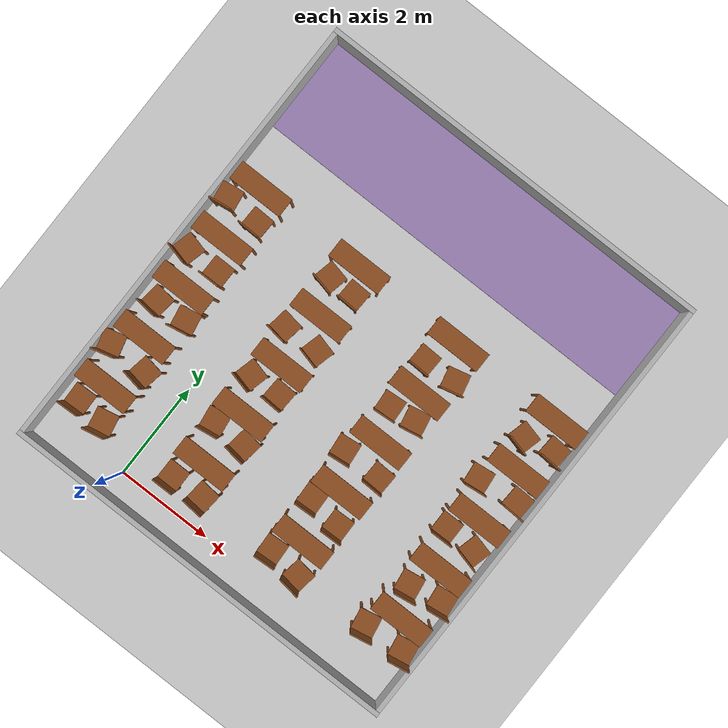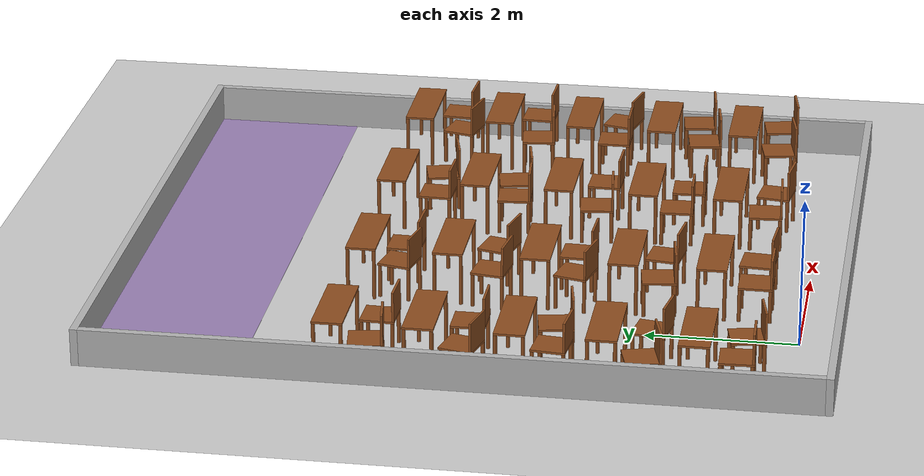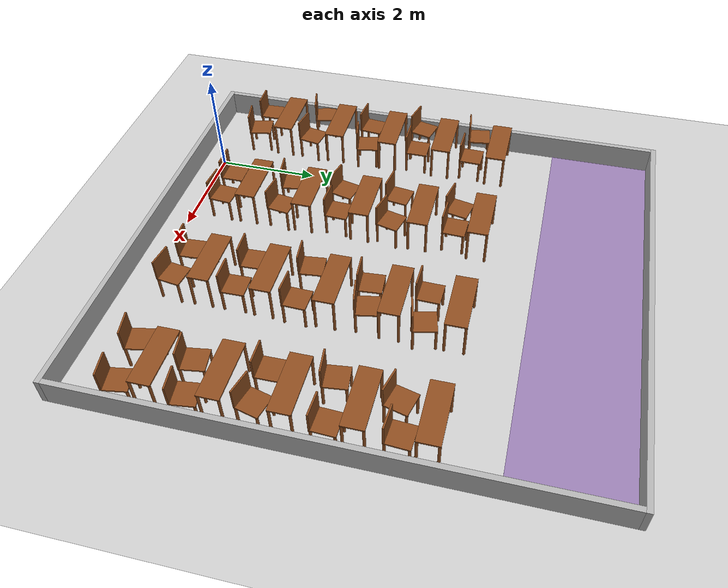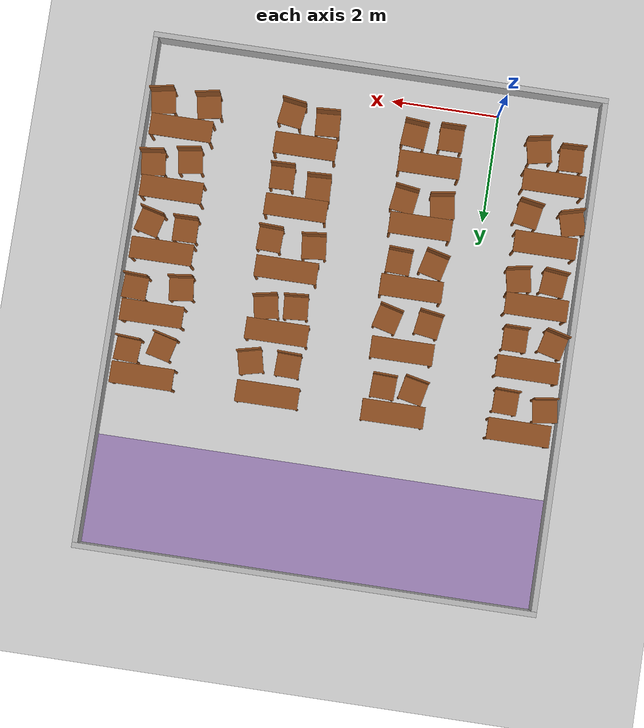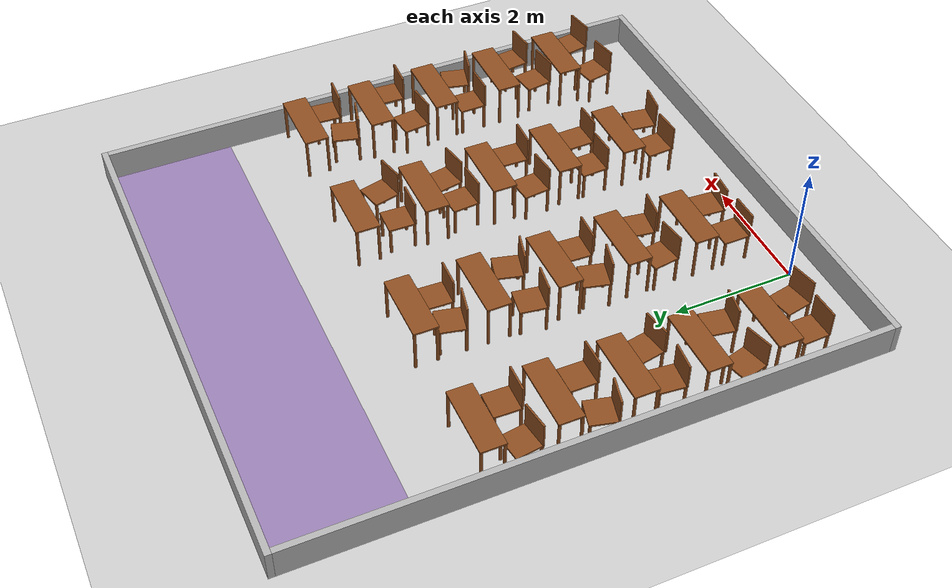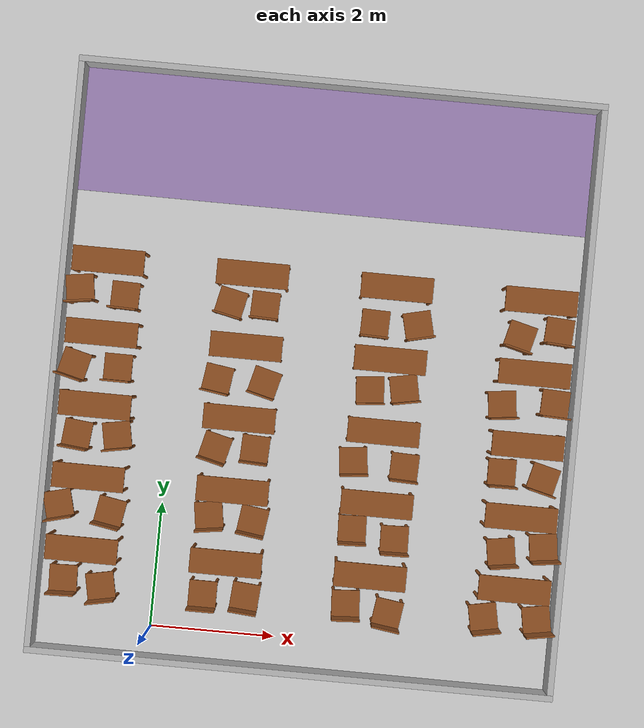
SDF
<?xml version="1.0"?>
<sdf version="1.6">
  <world name="lecture_hall_real">
    <!-- 모델 위치를 서비스로 바꿀 수 있게 (/set_entity_state): tools/sim_mover.py 로 움직이는 장애물 시험 -->
    <plugin name="gazebo_ros_state" filename="libgazebo_ros_state.so">
      <ros><namespace>/</namespace></ros>
      <update_rate>20.0</update_rate>
    </plugin>
    <include><uri>model://ground_plane</uri></include>
    <include><uri>model://sun</uri></include>
    <scene>
      <shadows>false</shadows>
    </scene>
    <physics type="ode">
      <real_time_update_rate>1000.0</real_time_update_rate>
      <max_step_size>0.001</max_step_size>
      <real_time_factor>1</real_time_factor>
    </physics>
    <model name="walls">
      <static>true</static>
      <link name="link">
        <collision name="c_s">
          <pose>2.300 -0.500 0.250 0 0 0</pose>
          <geometry><box><size>8.500 0.100 0.500</size></box></geometry>
        </collision>
        <visual name="v_s">
          <pose>2.300 -0.500 0.250 0 0 0</pose>
          <geometry><box><size>8.500 0.100 0.500</size></box></geometry>
          <material><ambient>0.6 0.6 0.6 1</ambient><diffuse>0.7 0.7 0.7 1</diffuse></material>
        </visual>
        <collision name="c_n">
          <pose>2.300 9.000 0.250 0 0 0</pose>
          <geometry><box><size>8.500 0.100 0.500</size></box></geometry>
        </collision>
        <visual name="v_n">
          <pose>2.300 9.000 0.250 0 0 0</pose>
          <geometry><box><size>8.500 0.100 0.500</size></box></geometry>
          <material><ambient>0.6 0.6 0.6 1</ambient><diffuse>0.7 0.7 0.7 1</diffuse></material>
        </visual>
        <collision name="c_w">
          <pose>-1.900 4.250 0.250 0 0 0</pose>
          <geometry><box><size>0.100 9.400 0.500</size></box></geometry>
        </collision>
        <visual name="v_w">
          <pose>-1.900 4.250 0.250 0 0 0</pose>
          <geometry><box><size>0.100 9.400 0.500</size></box></geometry>
          <material><ambient>0.6 0.6 0.6 1</ambient><diffuse>0.7 0.7 0.7 1</diffuse></material>
        </visual>
        <collision name="c_e">
          <pose>6.500 4.250 0.250 0 0 0</pose>
          <geometry><box><size>0.100 9.400 0.500</size></box></geometry>
        </collision>
        <visual name="v_e">
          <pose>6.500 4.250 0.250 0 0 0</pose>
          <geometry><box><size>0.100 9.400 0.500</size></box></geometry>
          <material><ambient>0.6 0.6 0.6 1</ambient><diffuse>0.7 0.7 0.7 1</diffuse></material>
        </visual>
        <visual name="v_stage">
          <pose>2.300 7.950 0.002 0 0 0</pose>
          <geometry><box><size>8.300 2.000 0.004</size></box></geometry>
          <material><ambient>0.5 0.4 0.6 1</ambient><diffuse>0.6 0.5 0.7 1</diffuse></material>
        </visual>
      </link>
    </model>
    <model name="desk_1_1">
      <static>true</static>
      <pose>-1.150 5.800 0 0 0 0</pose>
      <link name="link">
        <collision name="c_leg0">
          <pose>-0.550 -0.175 0.345 0 0 0</pose>
          <geometry><cylinder><radius>0.025</radius><length>0.690</length></cylinder></geometry>
        </collision>
        <visual name="v_leg0">
          <pose>-0.550 -0.175 0.345 0 0 0</pose>
          <geometry><cylinder><radius>0.025</radius><length>0.690</length></cylinder></geometry>
          <material><ambient>0.45 0.25 0.1 1</ambient><diffuse>0.55 0.3 0.12 1</diffuse></material>
        </visual>
        <collision name="c_leg1">
          <pose>-0.550 0.175 0.345 0 0 0</pose>
          <geometry><cylinder><radius>0.025</radius><length>0.690</length></cylinder></geometry>
        </collision>
        <visual name="v_leg1">
          <pose>-0.550 0.175 0.345 0 0 0</pose>
          <geometry><cylinder><radius>0.025</radius><length>0.690</length></cylinder></geometry>
          <material><ambient>0.45 0.25 0.1 1</ambient><diffuse>0.55 0.3 0.12 1</diffuse></material>
        </visual>
        <collision name="c_leg2">
          <pose>0.550 -0.175 0.345 0 0 0</pose>
          <geometry><cylinder><radius>0.025</radius><length>0.690</length></cylinder></geometry>
        </collision>
        <visual name="v_leg2">
          <pose>0.550 -0.175 0.345 0 0 0</pose>
          <geometry><cylinder><radius>0.025</radius><length>0.690</length></cylinder></geometry>
          <material><ambient>0.45 0.25 0.1 1</ambient><diffuse>0.55 0.3 0.12 1</diffuse></material>
        </visual>
        <collision name="c_leg3">
          <pose>0.550 0.175 0.345 0 0 0</pose>
          <geometry><cylinder><radius>0.025</radius><length>0.690</length></cylinder></geometry>
        </collision>
        <visual name="v_leg3">
          <pose>0.550 0.175 0.345 0 0 0</pose>
          <geometry><cylinder><radius>0.025</radius><length>0.690</length></cylinder></geometry>
          <material><ambient>0.45 0.25 0.1 1</ambient><diffuse>0.55 0.3 0.12 1</diffuse></material>
        </visual>
        <collision name="c_top">
          <pose>0.000 0.000 0.705 0 0 0</pose>
          <geometry><box><size>1.150 0.400 0.030</size></box></geometry>
        </collision>
        <visual name="v_top">
          <pose>0.000 0.000 0.705 0 0 0</pose>
          <geometry><box><size>1.150 0.400 0.030</size></box></geometry>
          <material><ambient>0.45 0.25 0.1 1</ambient><diffuse>0.55 0.3 0.12 1</diffuse></material>
        </visual>
      </link>
    </model>
    <model name="chair_1_1_1">
      <static>true</static>
      <pose>-1.588 5.332 0 0 0 0.138</pose>
      <link name="link">
        <collision name="c_leg0">
          <pose>-0.200 -0.200 0.225 0 0 0</pose>
          <geometry><cylinder><radius>0.025</radius><length>0.450</length></cylinder></geometry>
        </collision>
        <visual name="v_leg0">
          <pose>-0.200 -0.200 0.225 0 0 0</pose>
          <geometry><cylinder><radius>0.025</radius><length>0.450</length></cylinder></geometry>
          <material><ambient>0.45 0.25 0.1 1</ambient><diffuse>0.55 0.3 0.12 1</diffuse></material>
        </visual>
        <collision name="c_leg1">
          <pose>-0.200 0.200 0.225 0 0 0</pose>
          <geometry><cylinder><radius>0.025</radius><length>0.450</length></cylinder></geometry>
        </collision>
        <visual name="v_leg1">
          <pose>-0.200 0.200 0.225 0 0 0</pose>
          <geometry><cylinder><radius>0.025</radius><length>0.450</length></cylinder></geometry>
          <material><ambient>0.45 0.25 0.1 1</ambient><diffuse>0.55 0.3 0.12 1</diffuse></material>
        </visual>
        <collision name="c_leg2">
          <pose>0.200 -0.200 0.225 0 0 0</pose>
          <geometry><cylinder><radius>0.025</radius><length>0.450</length></cylinder></geometry>
        </collision>
        <visual name="v_leg2">
          <pose>0.200 -0.200 0.225 0 0 0</pose>
          <geometry><cylinder><radius>0.025</radius><length>0.450</length></cylinder></geometry>
          <material><ambient>0.45 0.25 0.1 1</ambient><diffuse>0.55 0.3 0.12 1</diffuse></material>
        </visual>
        <collision name="c_leg3">
          <pose>0.200 0.200 0.225 0 0 0</pose>
          <geometry><cylinder><radius>0.025</radius><length>0.450</length></cylinder></geometry>
        </collision>
        <visual name="v_leg3">
          <pose>0.200 0.200 0.225 0 0 0</pose>
          <geometry><cylinder><radius>0.025</radius><length>0.450</length></cylinder></geometry>
          <material><ambient>0.45 0.25 0.1 1</ambient><diffuse>0.55 0.3 0.12 1</diffuse></material>
        </visual>
        <collision name="c_seat">
          <pose>0.000 0.000 0.465 0 0 0</pose>
          <geometry><box><size>0.450 0.450 0.030</size></box></geometry>
        </collision>
        <visual name="v_seat">
          <pose>0.000 0.000 0.465 0 0 0</pose>
          <geometry><box><size>0.450 0.450 0.030</size></box></geometry>
          <material><ambient>0.45 0.25 0.1 1</ambient><diffuse>0.55 0.3 0.12 1</diffuse></material>
        </visual>
        <collision name="c_back">
          <pose>0.000 -0.210 0.680 0 0 0</pose>
          <geometry><box><size>0.450 0.030 0.400</size></box></geometry>
        </collision>
        <visual name="v_back">
          <pose>0.000 -0.210 0.680 0 0 0</pose>
          <geometry><box><size>0.450 0.030 0.400</size></box></geometry>
          <material><ambient>0.45 0.25 0.1 1</ambient><diffuse>0.55 0.3 0.12 1</diffuse></material>
        </visual>
      </link>
    </model>
    <model name="chair_1_1_2">
      <static>true</static>
      <pose>-0.859 5.279 0 0 0 -0.026</pose>
      <link name="link">
        <collision name="c_leg0">
          <pose>-0.200 -0.200 0.225 0 0 0</pose>
          <geometry><cylinder><radius>0.025</radius><length>0.450</length></cylinder></geometry>
        </collision>
        <visual name="v_leg0">
          <pose>-0.200 -0.200 0.225 0 0 0</pose>
          <geometry><cylinder><radius>0.025</radius><length>0.450</length></cylinder></geometry>
          <material><ambient>0.45 0.25 0.1 1</ambient><diffuse>0.55 0.3 0.12 1</diffuse></material>
        </visual>
        <collision name="c_leg1">
          <pose>-0.200 0.200 0.225 0 0 0</pose>
          <geometry><cylinder><radius>0.025</radius><length>0.450</length></cylinder></geometry>
        </collision>
        <visual name="v_leg1">
          <pose>-0.200 0.200 0.225 0 0 0</pose>
          <geometry><cylinder><radius>0.025</radius><length>0.450</length></cylinder></geometry>
          <material><ambient>0.45 0.25 0.1 1</ambient><diffuse>0.55 0.3 0.12 1</diffuse></material>
        </visual>
        <collision name="c_leg2">
          <pose>0.200 -0.200 0.225 0 0 0</pose>
          <geometry><cylinder><radius>0.025</radius><length>0.450</length></cylinder></geometry>
        </collision>
        <visual name="v_leg2">
          <pose>0.200 -0.200 0.225 0 0 0</pose>
          <geometry><cylinder><radius>0.025</radius><length>0.450</length></cylinder></geometry>
          <material><ambient>0.45 0.25 0.1 1</ambient><diffuse>0.55 0.3 0.12 1</diffuse></material>
        </visual>
        <collision name="c_leg3">
          <pose>0.200 0.200 0.225 0 0 0</pose>
          <geometry><cylinder><radius>0.025</radius><length>0.450</length></cylinder></geometry>
        </collision>
        <visual name="v_leg3">
          <pose>0.200 0.200 0.225 0 0 0</pose>
          <geometry><cylinder><radius>0.025</radius><length>0.450</length></cylinder></geometry>
          <material><ambient>0.45 0.25 0.1 1</ambient><diffuse>0.55 0.3 0.12 1</diffuse></material>
        </visual>
        <collision name="c_seat">
          <pose>0.000 0.000 0.465 0 0 0</pose>
          <geometry><box><size>0.450 0.450 0.030</size></box></geometry>
        </collision>
        <visual name="v_seat">
          <pose>0.000 0.000 0.465 0 0 0</pose>
          <geometry><box><size>0.450 0.450 0.030</size></box></geometry>
          <material><ambient>0.45 0.25 0.1 1</ambient><diffuse>0.55 0.3 0.12 1</diffuse></material>
        </visual>
        <collision name="c_back">
          <pose>0.000 -0.210 0.680 0 0 0</pose>
          <geometry><box><size>0.450 0.030 0.400</size></box></geometry>
        </collision>
        <visual name="v_back">
          <pose>0.000 -0.210 0.680 0 0 0</pose>
          <geometry><box><size>0.450 0.030 0.400</size></box></geometry>
          <material><ambient>0.45 0.25 0.1 1</ambient><diffuse>0.55 0.3 0.12 1</diffuse></material>
        </visual>
      </link>
    </model>
    <model name="desk_1_2">
      <static>true</static>
      <pose>1.150 5.800 0 0 0 0</pose>
      <link name="link">
        <collision name="c_leg0">
          <pose>-0.550 -0.175 0.345 0 0 0</pose>
          <geometry><cylinder><radius>0.025</radius><length>0.690</length></cylinder></geometry>
        </collision>
        <visual name="v_leg0">
          <pose>-0.550 -0.175 0.345 0 0 0</pose>
          <geometry><cylinder><radius>0.025</radius><length>0.690</length></cylinder></geometry>
          <material><ambient>0.45 0.25 0.1 1</ambient><diffuse>0.55 0.3 0.12 1</diffuse></material>
        </visual>
        <collision name="c_leg1">
          <pose>-0.550 0.175 0.345 0 0 0</pose>
          <geometry><cylinder><radius>0.025</radius><length>0.690</length></cylinder></geometry>
        </collision>
        <visual name="v_leg1">
          <pose>-0.550 0.175 0.345 0 0 0</pose>
          <geometry><cylinder><radius>0.025</radius><length>0.690</length></cylinder></geometry>
          <material><ambient>0.45 0.25 0.1 1</ambient><diffuse>0.55 0.3 0.12 1</diffuse></material>
        </visual>
        <collision name="c_leg2">
          <pose>0.550 -0.175 0.345 0 0 0</pose>
          <geometry><cylinder><radius>0.025</radius><length>0.690</length></cylinder></geometry>
        </collision>
        <visual name="v_leg2">
          <pose>0.550 -0.175 0.345 0 0 0</pose>
          <geometry><cylinder><radius>0.025</radius><length>0.690</length></cylinder></geometry>
          <material><ambient>0.45 0.25 0.1 1</ambient><diffuse>0.55 0.3 0.12 1</diffuse></material>
        </visual>
        <collision name="c_leg3">
          <pose>0.550 0.175 0.345 0 0 0</pose>
          <geometry><cylinder><radius>0.025</radius><length>0.690</length></cylinder></geometry>
        </collision>
        <visual name="v_leg3">
          <pose>0.550 0.175 0.345 0 0 0</pose>
          <geometry><cylinder><radius>0.025</radius><length>0.690</length></cylinder></geometry>
          <material><ambient>0.45 0.25 0.1 1</ambient><diffuse>0.55 0.3 0.12 1</diffuse></material>
        </visual>
        <collision name="c_top">
          <pose>0.000 0.000 0.705 0 0 0</pose>
          <geometry><box><size>1.150 0.400 0.030</size></box></geometry>
        </collision>
        <visual name="v_top">
          <pose>0.000 0.000 0.705 0 0 0</pose>
          <geometry><box><size>1.150 0.400 0.030</size></box></geometry>
          <material><ambient>0.45 0.25 0.1 1</ambient><diffuse>0.55 0.3 0.12 1</diffuse></material>
        </visual>
      </link>
    </model>
    <model name="chair_1_2_1">
      <static>true</static>
      <pose>0.836 5.323 0 0 0 -0.213</pose>
      <link name="link">
        <collision name="c_leg0">
          <pose>-0.200 -0.200 0.225 0 0 0</pose>
          <geometry><cylinder><radius>0.025</radius><length>0.450</length></cylinder></geometry>
        </collision>
        <visual name="v_leg0">
          <pose>-0.200 -0.200 0.225 0 0 0</pose>
          <geometry><cylinder><radius>0.025</radius><length>0.450</length></cylinder></geometry>
          <material><ambient>0.45 0.25 0.1 1</ambient><diffuse>0.55 0.3 0.12 1</diffuse></material>
        </visual>
        <collision name="c_leg1">
          <pose>-0.200 0.200 0.225 0 0 0</pose>
          <geometry><cylinder><radius>0.025</radius><length>0.450</length></cylinder></geometry>
        </collision>
        <visual name="v_leg1">
          <pose>-0.200 0.200 0.225 0 0 0</pose>
          <geometry><cylinder><radius>0.025</radius><length>0.450</length></cylinder></geometry>
          <material><ambient>0.45 0.25 0.1 1</ambient><diffuse>0.55 0.3 0.12 1</diffuse></material>
        </visual>
        <collision name="c_leg2">
          <pose>0.200 -0.200 0.225 0 0 0</pose>
          <geometry><cylinder><radius>0.025</radius><length>0.450</length></cylinder></geometry>
        </collision>
        <visual name="v_leg2">
          <pose>0.200 -0.200 0.225 0 0 0</pose>
          <geometry><cylinder><radius>0.025</radius><length>0.450</length></cylinder></geometry>
          <material><ambient>0.45 0.25 0.1 1</ambient><diffuse>0.55 0.3 0.12 1</diffuse></material>
        </visual>
        <collision name="c_leg3">
          <pose>0.200 0.200 0.225 0 0 0</pose>
          <geometry><cylinder><radius>0.025</radius><length>0.450</length></cylinder></geometry>
        </collision>
        <visual name="v_leg3">
          <pose>0.200 0.200 0.225 0 0 0</pose>
          <geometry><cylinder><radius>0.025</radius><length>0.450</length></cylinder></geometry>
          <material><ambient>0.45 0.25 0.1 1</ambient><diffuse>0.55 0.3 0.12 1</diffuse></material>
        </visual>
        <collision name="c_seat">
          <pose>0.000 0.000 0.465 0 0 0</pose>
          <geometry><box><size>0.450 0.450 0.030</size></box></geometry>
        </collision>
        <visual name="v_seat">
          <pose>0.000 0.000 0.465 0 0 0</pose>
          <geometry><box><size>0.450 0.450 0.030</size></box></geometry>
          <material><ambient>0.45 0.25 0.1 1</ambient><diffuse>0.55 0.3 0.12 1</diffuse></material>
        </visual>
        <collision name="c_back">
          <pose>0.000 -0.210 0.680 0 0 0</pose>
          <geometry><box><size>0.450 0.030 0.400</size></box></geometry>
        </collision>
        <visual name="v_back">
          <pose>0.000 -0.210 0.680 0 0 0</pose>
          <geometry><box><size>0.450 0.030 0.400</size></box></geometry>
          <material><ambient>0.45 0.25 0.1 1</ambient><diffuse>0.55 0.3 0.12 1</diffuse></material>
        </visual>
      </link>
    </model>
    <model name="chair_1_2_2">
      <static>true</static>
      <pose>1.387 5.330 0 0 0 -0.035</pose>
      <link name="link">
        <collision name="c_leg0">
          <pose>-0.200 -0.200 0.225 0 0 0</pose>
          <geometry><cylinder><radius>0.025</radius><length>0.450</length></cylinder></geometry>
        </collision>
        <visual name="v_leg0">
          <pose>-0.200 -0.200 0.225 0 0 0</pose>
          <geometry><cylinder><radius>0.025</radius><length>0.450</length></cylinder></geometry>
          <material><ambient>0.45 0.25 0.1 1</ambient><diffuse>0.55 0.3 0.12 1</diffuse></material>
        </visual>
        <collision name="c_leg1">
          <pose>-0.200 0.200 0.225 0 0 0</pose>
          <geometry><cylinder><radius>0.025</radius><length>0.450</length></cylinder></geometry>
        </collision>
        <visual name="v_leg1">
          <pose>-0.200 0.200 0.225 0 0 0</pose>
          <geometry><cylinder><radius>0.025</radius><length>0.450</length></cylinder></geometry>
          <material><ambient>0.45 0.25 0.1 1</ambient><diffuse>0.55 0.3 0.12 1</diffuse></material>
        </visual>
        <collision name="c_leg2">
          <pose>0.200 -0.200 0.225 0 0 0</pose>
          <geometry><cylinder><radius>0.025</radius><length>0.450</length></cylinder></geometry>
        </collision>
        <visual name="v_leg2">
          <pose>0.200 -0.200 0.225 0 0 0</pose>
          <geometry><cylinder><radius>0.025</radius><length>0.450</length></cylinder></geometry>
          <material><ambient>0.45 0.25 0.1 1</ambient><diffuse>0.55 0.3 0.12 1</diffuse></material>
        </visual>
        <collision name="c_leg3">
          <pose>0.200 0.200 0.225 0 0 0</pose>
          <geometry><cylinder><radius>0.025</radius><length>0.450</length></cylinder></geometry>
        </collision>
        <visual name="v_leg3">
          <pose>0.200 0.200 0.225 0 0 0</pose>
          <geometry><cylinder><radius>0.025</radius><length>0.450</length></cylinder></geometry>
          <material><ambient>0.45 0.25 0.1 1</ambient><diffuse>0.55 0.3 0.12 1</diffuse></material>
        </visual>
        <collision name="c_seat">
          <pose>0.000 0.000 0.465 0 0 0</pose>
          <geometry><box><size>0.450 0.450 0.030</size></box></geometry>
        </collision>
        <visual name="v_seat">
          <pose>0.000 0.000 0.465 0 0 0</pose>
          <geometry><box><size>0.450 0.450 0.030</size></box></geometry>
          <material><ambient>0.45 0.25 0.1 1</ambient><diffuse>0.55 0.3 0.12 1</diffuse></material>
        </visual>
        <collision name="c_back">
          <pose>0.000 -0.210 0.680 0 0 0</pose>
          <geometry><box><size>0.450 0.030 0.400</size></box></geometry>
        </collision>
        <visual name="v_back">
          <pose>0.000 -0.210 0.680 0 0 0</pose>
          <geometry><box><size>0.450 0.030 0.400</size></box></geometry>
          <material><ambient>0.45 0.25 0.1 1</ambient><diffuse>0.55 0.3 0.12 1</diffuse></material>
        </visual>
      </link>
    </model>
    <model name="desk_1_3">
      <static>true</static>
      <pose>3.450 5.800 0 0 0 0</pose>
      <link name="link">
        <collision name="c_leg0">
          <pose>-0.550 -0.175 0.345 0 0 0</pose>
          <geometry><cylinder><radius>0.025</radius><length>0.690</length></cylinder></geometry>
        </collision>
        <visual name="v_leg0">
          <pose>-0.550 -0.175 0.345 0 0 0</pose>
          <geometry><cylinder><radius>0.025</radius><length>0.690</length></cylinder></geometry>
          <material><ambient>0.45 0.25 0.1 1</ambient><diffuse>0.55 0.3 0.12 1</diffuse></material>
        </visual>
        <collision name="c_leg1">
          <pose>-0.550 0.175 0.345 0 0 0</pose>
          <geometry><cylinder><radius>0.025</radius><length>0.690</length></cylinder></geometry>
        </collision>
        <visual name="v_leg1">
          <pose>-0.550 0.175 0.345 0 0 0</pose>
          <geometry><cylinder><radius>0.025</radius><length>0.690</length></cylinder></geometry>
          <material><ambient>0.45 0.25 0.1 1</ambient><diffuse>0.55 0.3 0.12 1</diffuse></material>
        </visual>
        <collision name="c_leg2">
          <pose>0.550 -0.175 0.345 0 0 0</pose>
          <geometry><cylinder><radius>0.025</radius><length>0.690</length></cylinder></geometry>
        </collision>
        <visual name="v_leg2">
          <pose>0.550 -0.175 0.345 0 0 0</pose>
          <geometry><cylinder><radius>0.025</radius><length>0.690</length></cylinder></geometry>
          <material><ambient>0.45 0.25 0.1 1</ambient><diffuse>0.55 0.3 0.12 1</diffuse></material>
        </visual>
        <collision name="c_leg3">
          <pose>0.550 0.175 0.345 0 0 0</pose>
          <geometry><cylinder><radius>0.025</radius><length>0.690</length></cylinder></geometry>
        </collision>
        <visual name="v_leg3">
          <pose>0.550 0.175 0.345 0 0 0</pose>
          <geometry><cylinder><radius>0.025</radius><length>0.690</length></cylinder></geometry>
          <material><ambient>0.45 0.25 0.1 1</ambient><diffuse>0.55 0.3 0.12 1</diffuse></material>
        </visual>
        <collision name="c_top">
          <pose>0.000 0.000 0.705 0 0 0</pose>
          <geometry><box><size>1.150 0.400 0.030</size></box></geometry>
        </collision>
        <visual name="v_top">
          <pose>0.000 0.000 0.705 0 0 0</pose>
          <geometry><box><size>1.150 0.400 0.030</size></box></geometry>
          <material><ambient>0.45 0.25 0.1 1</ambient><diffuse>0.55 0.3 0.12 1</diffuse></material>
        </visual>
      </link>
    </model>
    <model name="chair_1_3_1">
      <static>true</static>
      <pose>3.163 5.205 0 0 0 -0.029</pose>
      <link name="link">
        <collision name="c_leg0">
          <pose>-0.200 -0.200 0.225 0 0 0</pose>
          <geometry><cylinder><radius>0.025</radius><length>0.450</length></cylinder></geometry>
        </collision>
        <visual name="v_leg0">
          <pose>-0.200 -0.200 0.225 0 0 0</pose>
          <geometry><cylinder><radius>0.025</radius><length>0.450</length></cylinder></geometry>
          <material><ambient>0.45 0.25 0.1 1</ambient><diffuse>0.55 0.3 0.12 1</diffuse></material>
        </visual>
        <collision name="c_leg1">
          <pose>-0.200 0.200 0.225 0 0 0</pose>
          <geometry><cylinder><radius>0.025</radius><length>0.450</length></cylinder></geometry>
        </collision>
        <visual name="v_leg1">
          <pose>-0.200 0.200 0.225 0 0 0</pose>
          <geometry><cylinder><radius>0.025</radius><length>0.450</length></cylinder></geometry>
          <material><ambient>0.45 0.25 0.1 1</ambient><diffuse>0.55 0.3 0.12 1</diffuse></material>
        </visual>
        <collision name="c_leg2">
          <pose>0.200 -0.200 0.225 0 0 0</pose>
          <geometry><cylinder><radius>0.025</radius><length>0.450</length></cylinder></geometry>
        </collision>
        <visual name="v_leg2">
          <pose>0.200 -0.200 0.225 0 0 0</pose>
          <geometry><cylinder><radius>0.025</radius><length>0.450</length></cylinder></geometry>
          <material><ambient>0.45 0.25 0.1 1</ambient><diffuse>0.55 0.3 0.12 1</diffuse></material>
        </visual>
        <collision name="c_leg3">
          <pose>0.200 0.200 0.225 0 0 0</pose>
          <geometry><cylinder><radius>0.025</radius><length>0.450</length></cylinder></geometry>
        </collision>
        <visual name="v_leg3">
          <pose>0.200 0.200 0.225 0 0 0</pose>
          <geometry><cylinder><radius>0.025</radius><length>0.450</length></cylinder></geometry>
          <material><ambient>0.45 0.25 0.1 1</ambient><diffuse>0.55 0.3 0.12 1</diffuse></material>
        </visual>
        <collision name="c_seat">
          <pose>0.000 0.000 0.465 0 0 0</pose>
          <geometry><box><size>0.450 0.450 0.030</size></box></geometry>
        </collision>
        <visual name="v_seat">
          <pose>0.000 0.000 0.465 0 0 0</pose>
          <geometry><box><size>0.450 0.450 0.030</size></box></geometry>
          <material><ambient>0.45 0.25 0.1 1</ambient><diffuse>0.55 0.3 0.12 1</diffuse></material>
        </visual>
        <collision name="c_back">
          <pose>0.000 -0.210 0.680 0 0 0</pose>
          <geometry><box><size>0.450 0.030 0.400</size></box></geometry>
        </collision>
        <visual name="v_back">
          <pose>0.000 -0.210 0.680 0 0 0</pose>
          <geometry><box><size>0.450 0.030 0.400</size></box></geometry>
          <material><ambient>0.45 0.25 0.1 1</ambient><diffuse>0.55 0.3 0.12 1</diffuse></material>
        </visual>
      </link>
    </model>
    <model name="chair_1_3_2">
      <static>true</static>
      <pose>3.853 5.239 0 0 0 0.233</pose>
      <link name="link">
        <collision name="c_leg0">
          <pose>-0.200 -0.200 0.225 0 0 0</pose>
          <geometry><cylinder><radius>0.025</radius><length>0.450</length></cylinder></geometry>
        </collision>
        <visual name="v_leg0">
          <pose>-0.200 -0.200 0.225 0 0 0</pose>
          <geometry><cylinder><radius>0.025</radius><length>0.450</length></cylinder></geometry>
          <material><ambient>0.45 0.25 0.1 1</ambient><diffuse>0.55 0.3 0.12 1</diffuse></material>
        </visual>
        <collision name="c_leg1">
          <pose>-0.200 0.200 0.225 0 0 0</pose>
          <geometry><cylinder><radius>0.025</radius><length>0.450</length></cylinder></geometry>
        </collision>
        <visual name="v_leg1">
          <pose>-0.200 0.200 0.225 0 0 0</pose>
          <geometry><cylinder><radius>0.025</radius><length>0.450</length></cylinder></geometry>
          <material><ambient>0.45 0.25 0.1 1</ambient><diffuse>0.55 0.3 0.12 1</diffuse></material>
        </visual>
        <collision name="c_leg2">
          <pose>0.200 -0.200 0.225 0 0 0</pose>
          <geometry><cylinder><radius>0.025</radius><length>0.450</length></cylinder></geometry>
        </collision>
        <visual name="v_leg2">
          <pose>0.200 -0.200 0.225 0 0 0</pose>
          <geometry><cylinder><radius>0.025</radius><length>0.450</length></cylinder></geometry>
          <material><ambient>0.45 0.25 0.1 1</ambient><diffuse>0.55 0.3 0.12 1</diffuse></material>
        </visual>
        <collision name="c_leg3">
          <pose>0.200 0.200 0.225 0 0 0</pose>
          <geometry><cylinder><radius>0.025</radius><length>0.450</length></cylinder></geometry>
        </collision>
        <visual name="v_leg3">
          <pose>0.200 0.200 0.225 0 0 0</pose>
          <geometry><cylinder><radius>0.025</radius><length>0.450</length></cylinder></geometry>
          <material><ambient>0.45 0.25 0.1 1</ambient><diffuse>0.55 0.3 0.12 1</diffuse></material>
        </visual>
        <collision name="c_seat">
          <pose>0.000 0.000 0.465 0 0 0</pose>
          <geometry><box><size>0.450 0.450 0.030</size></box></geometry>
        </collision>
        <visual name="v_seat">
          <pose>0.000 0.000 0.465 0 0 0</pose>
          <geometry><box><size>0.450 0.450 0.030</size></box></geometry>
          <material><ambient>0.45 0.25 0.1 1</ambient><diffuse>0.55 0.3 0.12 1</diffuse></material>
        </visual>
        <collision name="c_back">
          <pose>0.000 -0.210 0.680 0 0 0</pose>
          <geometry><box><size>0.450 0.030 0.400</size></box></geometry>
        </collision>
        <visual name="v_back">
          <pose>0.000 -0.210 0.680 0 0 0</pose>
          <geometry><box><size>0.450 0.030 0.400</size></box></geometry>
          <material><ambient>0.45 0.25 0.1 1</ambient><diffuse>0.55 0.3 0.12 1</diffuse></material>
        </visual>
      </link>
    </model>
    <model name="desk_1_4">
      <static>true</static>
      <pose>5.750 5.800 0 0 0 0</pose>
      <link name="link">
        <collision name="c_leg0">
          <pose>-0.550 -0.175 0.345 0 0 0</pose>
          <geometry><cylinder><radius>0.025</radius><length>0.690</length></cylinder></geometry>
        </collision>
        <visual name="v_leg0">
          <pose>-0.550 -0.175 0.345 0 0 0</pose>
          <geometry><cylinder><radius>0.025</radius><length>0.690</length></cylinder></geometry>
          <material><ambient>0.45 0.25 0.1 1</ambient><diffuse>0.55 0.3 0.12 1</diffuse></material>
        </visual>
        <collision name="c_leg1">
          <pose>-0.550 0.175 0.345 0 0 0</pose>
          <geometry><cylinder><radius>0.025</radius><length>0.690</length></cylinder></geometry>
        </collision>
        <visual name="v_leg1">
          <pose>-0.550 0.175 0.345 0 0 0</pose>
          <geometry><cylinder><radius>0.025</radius><length>0.690</length></cylinder></geometry>
          <material><ambient>0.45 0.25 0.1 1</ambient><diffuse>0.55 0.3 0.12 1</diffuse></material>
        </visual>
        <collision name="c_leg2">
          <pose>0.550 -0.175 0.345 0 0 0</pose>
          <geometry><cylinder><radius>0.025</radius><length>0.690</length></cylinder></geometry>
        </collision>
        <visual name="v_leg2">
          <pose>0.550 -0.175 0.345 0 0 0</pose>
          <geometry><cylinder><radius>0.025</radius><length>0.690</length></cylinder></geometry>
          <material><ambient>0.45 0.25 0.1 1</ambient><diffuse>0.55 0.3 0.12 1</diffuse></material>
        </visual>
        <collision name="c_leg3">
          <pose>0.550 0.175 0.345 0 0 0</pose>
          <geometry><cylinder><radius>0.025</radius><length>0.690</length></cylinder></geometry>
        </collision>
        <visual name="v_leg3">
          <pose>0.550 0.175 0.345 0 0 0</pose>
          <geometry><cylinder><radius>0.025</radius><length>0.690</length></cylinder></geometry>
          <material><ambient>0.45 0.25 0.1 1</ambient><diffuse>0.55 0.3 0.12 1</diffuse></material>
        </visual>
        <collision name="c_top">
          <pose>0.000 0.000 0.705 0 0 0</pose>
          <geometry><box><size>1.150 0.400 0.030</size></box></geometry>
        </collision>
        <visual name="v_top">
          <pose>0.000 0.000 0.705 0 0 0</pose>
          <geometry><box><size>1.150 0.400 0.030</size></box></geometry>
          <material><ambient>0.45 0.25 0.1 1</ambient><diffuse>0.55 0.3 0.12 1</diffuse></material>
        </visual>
      </link>
    </model>
    <model name="chair_1_4_1">
      <static>true</static>
      <pose>5.496 5.210 0 0 0 -0.248</pose>
      <link name="link">
        <collision name="c_leg0">
          <pose>-0.200 -0.200 0.225 0 0 0</pose>
          <geometry><cylinder><radius>0.025</radius><length>0.450</length></cylinder></geometry>
        </collision>
        <visual name="v_leg0">
          <pose>-0.200 -0.200 0.225 0 0 0</pose>
          <geometry><cylinder><radius>0.025</radius><length>0.450</length></cylinder></geometry>
          <material><ambient>0.45 0.25 0.1 1</ambient><diffuse>0.55 0.3 0.12 1</diffuse></material>
        </visual>
        <collision name="c_leg1">
          <pose>-0.200 0.200 0.225 0 0 0</pose>
          <geometry><cylinder><radius>0.025</radius><length>0.450</length></cylinder></geometry>
        </collision>
        <visual name="v_leg1">
          <pose>-0.200 0.200 0.225 0 0 0</pose>
          <geometry><cylinder><radius>0.025</radius><length>0.450</length></cylinder></geometry>
          <material><ambient>0.45 0.25 0.1 1</ambient><diffuse>0.55 0.3 0.12 1</diffuse></material>
        </visual>
        <collision name="c_leg2">
          <pose>0.200 -0.200 0.225 0 0 0</pose>
          <geometry><cylinder><radius>0.025</radius><length>0.450</length></cylinder></geometry>
        </collision>
        <visual name="v_leg2">
          <pose>0.200 -0.200 0.225 0 0 0</pose>
          <geometry><cylinder><radius>0.025</radius><length>0.450</length></cylinder></geometry>
          <material><ambient>0.45 0.25 0.1 1</ambient><diffuse>0.55 0.3 0.12 1</diffuse></material>
        </visual>
        <collision name="c_leg3">
          <pose>0.200 0.200 0.225 0 0 0</pose>
          <geometry><cylinder><radius>0.025</radius><length>0.450</length></cylinder></geometry>
        </collision>
        <visual name="v_leg3">
          <pose>0.200 0.200 0.225 0 0 0</pose>
          <geometry><cylinder><radius>0.025</radius><length>0.450</length></cylinder></geometry>
          <material><ambient>0.45 0.25 0.1 1</ambient><diffuse>0.55 0.3 0.12 1</diffuse></material>
        </visual>
        <collision name="c_seat">
          <pose>0.000 0.000 0.465 0 0 0</pose>
          <geometry><box><size>0.450 0.450 0.030</size></box></geometry>
        </collision>
        <visual name="v_seat">
          <pose>0.000 0.000 0.465 0 0 0</pose>
          <geometry><box><size>0.450 0.450 0.030</size></box></geometry>
          <material><ambient>0.45 0.25 0.1 1</ambient><diffuse>0.55 0.3 0.12 1</diffuse></material>
        </visual>
        <collision name="c_back">
          <pose>0.000 -0.210 0.680 0 0 0</pose>
          <geometry><box><size>0.450 0.030 0.400</size></box></geometry>
        </collision>
        <visual name="v_back">
          <pose>0.000 -0.210 0.680 0 0 0</pose>
          <geometry><box><size>0.450 0.030 0.400</size></box></geometry>
          <material><ambient>0.45 0.25 0.1 1</ambient><diffuse>0.55 0.3 0.12 1</diffuse></material>
        </visual>
      </link>
    </model>
    <model name="chair_1_4_2">
      <static>true</static>
      <pose>6.110 5.346 0 0 0 -0.062</pose>
      <link name="link">
        <collision name="c_leg0">
          <pose>-0.200 -0.200 0.225 0 0 0</pose>
          <geometry><cylinder><radius>0.025</radius><length>0.450</length></cylinder></geometry>
        </collision>
        <visual name="v_leg0">
          <pose>-0.200 -0.200 0.225 0 0 0</pose>
          <geometry><cylinder><radius>0.025</radius><length>0.450</length></cylinder></geometry>
          <material><ambient>0.45 0.25 0.1 1</ambient><diffuse>0.55 0.3 0.12 1</diffuse></material>
        </visual>
        <collision name="c_leg1">
          <pose>-0.200 0.200 0.225 0 0 0</pose>
          <geometry><cylinder><radius>0.025</radius><length>0.450</length></cylinder></geometry>
        </collision>
        <visual name="v_leg1">
          <pose>-0.200 0.200 0.225 0 0 0</pose>
          <geometry><cylinder><radius>0.025</radius><length>0.450</length></cylinder></geometry>
          <material><ambient>0.45 0.25 0.1 1</ambient><diffuse>0.55 0.3 0.12 1</diffuse></material>
        </visual>
        <collision name="c_leg2">
          <pose>0.200 -0.200 0.225 0 0 0</pose>
          <geometry><cylinder><radius>0.025</radius><length>0.450</length></cylinder></geometry>
        </collision>
        <visual name="v_leg2">
          <pose>0.200 -0.200 0.225 0 0 0</pose>
          <geometry><cylinder><radius>0.025</radius><length>0.450</length></cylinder></geometry>
          <material><ambient>0.45 0.25 0.1 1</ambient><diffuse>0.55 0.3 0.12 1</diffuse></material>
        </visual>
        <collision name="c_leg3">
          <pose>0.200 0.200 0.225 0 0 0</pose>
          <geometry><cylinder><radius>0.025</radius><length>0.450</length></cylinder></geometry>
        </collision>
        <visual name="v_leg3">
          <pose>0.200 0.200 0.225 0 0 0</pose>
          <geometry><cylinder><radius>0.025</radius><length>0.450</length></cylinder></geometry>
          <material><ambient>0.45 0.25 0.1 1</ambient><diffuse>0.55 0.3 0.12 1</diffuse></material>
        </visual>
        <collision name="c_seat">
          <pose>0.000 0.000 0.465 0 0 0</pose>
          <geometry><box><size>0.450 0.450 0.030</size></box></geometry>
        </collision>
        <visual name="v_seat">
          <pose>0.000 0.000 0.465 0 0 0</pose>
          <geometry><box><size>0.450 0.450 0.030</size></box></geometry>
          <material><ambient>0.45 0.25 0.1 1</ambient><diffuse>0.55 0.3 0.12 1</diffuse></material>
        </visual>
        <collision name="c_back">
          <pose>0.000 -0.210 0.680 0 0 0</pose>
          <geometry><box><size>0.450 0.030 0.400</size></box></geometry>
        </collision>
        <visual name="v_back">
          <pose>0.000 -0.210 0.680 0 0 0</pose>
          <geometry><box><size>0.450 0.030 0.400</size></box></geometry>
          <material><ambient>0.45 0.25 0.1 1</ambient><diffuse>0.55 0.3 0.12 1</diffuse></material>
        </visual>
      </link>
    </model>
    <model name="desk_2_1">
      <static>true</static>
      <pose>-1.150 4.650 0 0 0 0</pose>
      <link name="link">
        <collision name="c_leg0">
          <pose>-0.550 -0.175 0.345 0 0 0</pose>
          <geometry><cylinder><radius>0.025</radius><length>0.690</length></cylinder></geometry>
        </collision>
        <visual name="v_leg0">
          <pose>-0.550 -0.175 0.345 0 0 0</pose>
          <geometry><cylinder><radius>0.025</radius><length>0.690</length></cylinder></geometry>
          <material><ambient>0.45 0.25 0.1 1</ambient><diffuse>0.55 0.3 0.12 1</diffuse></material>
        </visual>
        <collision name="c_leg1">
          <pose>-0.550 0.175 0.345 0 0 0</pose>
          <geometry><cylinder><radius>0.025</radius><length>0.690</length></cylinder></geometry>
        </collision>
        <visual name="v_leg1">
          <pose>-0.550 0.175 0.345 0 0 0</pose>
          <geometry><cylinder><radius>0.025</radius><length>0.690</length></cylinder></geometry>
          <material><ambient>0.45 0.25 0.1 1</ambient><diffuse>0.55 0.3 0.12 1</diffuse></material>
        </visual>
        <collision name="c_leg2">
          <pose>0.550 -0.175 0.345 0 0 0</pose>
          <geometry><cylinder><radius>0.025</radius><length>0.690</length></cylinder></geometry>
        </collision>
        <visual name="v_leg2">
          <pose>0.550 -0.175 0.345 0 0 0</pose>
          <geometry><cylinder><radius>0.025</radius><length>0.690</length></cylinder></geometry>
          <material><ambient>0.45 0.25 0.1 1</ambient><diffuse>0.55 0.3 0.12 1</diffuse></material>
        </visual>
        <collision name="c_leg3">
          <pose>0.550 0.175 0.345 0 0 0</pose>
          <geometry><cylinder><radius>0.025</radius><length>0.690</length></cylinder></geometry>
        </collision>
        <visual name="v_leg3">
          <pose>0.550 0.175 0.345 0 0 0</pose>
          <geometry><cylinder><radius>0.025</radius><length>0.690</length></cylinder></geometry>
          <material><ambient>0.45 0.25 0.1 1</ambient><diffuse>0.55 0.3 0.12 1</diffuse></material>
        </visual>
        <collision name="c_top">
          <pose>0.000 0.000 0.705 0 0 0</pose>
          <geometry><box><size>1.150 0.400 0.030</size></box></geometry>
        </collision>
        <visual name="v_top">
          <pose>0.000 0.000 0.705 0 0 0</pose>
          <geometry><box><size>1.150 0.400 0.030</size></box></geometry>
          <material><ambient>0.45 0.25 0.1 1</ambient><diffuse>0.55 0.3 0.12 1</diffuse></material>
        </visual>
      </link>
    </model>
    <model name="chair_2_1_1">
      <static>true</static>
      <pose>-1.568 4.118 0 0 0 -0.247</pose>
      <link name="link">
        <collision name="c_leg0">
          <pose>-0.200 -0.200 0.225 0 0 0</pose>
          <geometry><cylinder><radius>0.025</radius><length>0.450</length></cylinder></geometry>
        </collision>
        <visual name="v_leg0">
          <pose>-0.200 -0.200 0.225 0 0 0</pose>
          <geometry><cylinder><radius>0.025</radius><length>0.450</length></cylinder></geometry>
          <material><ambient>0.45 0.25 0.1 1</ambient><diffuse>0.55 0.3 0.12 1</diffuse></material>
        </visual>
        <collision name="c_leg1">
          <pose>-0.200 0.200 0.225 0 0 0</pose>
          <geometry><cylinder><radius>0.025</radius><length>0.450</length></cylinder></geometry>
        </collision>
        <visual name="v_leg1">
          <pose>-0.200 0.200 0.225 0 0 0</pose>
          <geometry><cylinder><radius>0.025</radius><length>0.450</length></cylinder></geometry>
          <material><ambient>0.45 0.25 0.1 1</ambient><diffuse>0.55 0.3 0.12 1</diffuse></material>
        </visual>
        <collision name="c_leg2">
          <pose>0.200 -0.200 0.225 0 0 0</pose>
          <geometry><cylinder><radius>0.025</radius><length>0.450</length></cylinder></geometry>
        </collision>
        <visual name="v_leg2">
          <pose>0.200 -0.200 0.225 0 0 0</pose>
          <geometry><cylinder><radius>0.025</radius><length>0.450</length></cylinder></geometry>
          <material><ambient>0.45 0.25 0.1 1</ambient><diffuse>0.55 0.3 0.12 1</diffuse></material>
        </visual>
        <collision name="c_leg3">
          <pose>0.200 0.200 0.225 0 0 0</pose>
          <geometry><cylinder><radius>0.025</radius><length>0.450</length></cylinder></geometry>
        </collision>
        <visual name="v_leg3">
          <pose>0.200 0.200 0.225 0 0 0</pose>
          <geometry><cylinder><radius>0.025</radius><length>0.450</length></cylinder></geometry>
          <material><ambient>0.45 0.25 0.1 1</ambient><diffuse>0.55 0.3 0.12 1</diffuse></material>
        </visual>
        <collision name="c_seat">
          <pose>0.000 0.000 0.465 0 0 0</pose>
          <geometry><box><size>0.450 0.450 0.030</size></box></geometry>
        </collision>
        <visual name="v_seat">
          <pose>0.000 0.000 0.465 0 0 0</pose>
          <geometry><box><size>0.450 0.450 0.030</size></box></geometry>
          <material><ambient>0.45 0.25 0.1 1</ambient><diffuse>0.55 0.3 0.12 1</diffuse></material>
        </visual>
        <collision name="c_back">
          <pose>0.000 -0.210 0.680 0 0 0</pose>
          <geometry><box><size>0.450 0.030 0.400</size></box></geometry>
        </collision>
        <visual name="v_back">
          <pose>0.000 -0.210 0.680 0 0 0</pose>
          <geometry><box><size>0.450 0.030 0.400</size></box></geometry>
          <material><ambient>0.45 0.25 0.1 1</ambient><diffuse>0.55 0.3 0.12 1</diffuse></material>
        </visual>
      </link>
    </model>
    <model name="chair_2_1_2">
      <static>true</static>
      <pose>-0.867 4.121 0 0 0 -0.002</pose>
      <link name="link">
        <collision name="c_leg0">
          <pose>-0.200 -0.200 0.225 0 0 0</pose>
          <geometry><cylinder><radius>0.025</radius><length>0.450</length></cylinder></geometry>
        </collision>
        <visual name="v_leg0">
          <pose>-0.200 -0.200 0.225 0 0 0</pose>
          <geometry><cylinder><radius>0.025</radius><length>0.450</length></cylinder></geometry>
          <material><ambient>0.45 0.25 0.1 1</ambient><diffuse>0.55 0.3 0.12 1</diffuse></material>
        </visual>
        <collision name="c_leg1">
          <pose>-0.200 0.200 0.225 0 0 0</pose>
          <geometry><cylinder><radius>0.025</radius><length>0.450</length></cylinder></geometry>
        </collision>
        <visual name="v_leg1">
          <pose>-0.200 0.200 0.225 0 0 0</pose>
          <geometry><cylinder><radius>0.025</radius><length>0.450</length></cylinder></geometry>
          <material><ambient>0.45 0.25 0.1 1</ambient><diffuse>0.55 0.3 0.12 1</diffuse></material>
        </visual>
        <collision name="c_leg2">
          <pose>0.200 -0.200 0.225 0 0 0</pose>
          <geometry><cylinder><radius>0.025</radius><length>0.450</length></cylinder></geometry>
        </collision>
        <visual name="v_leg2">
          <pose>0.200 -0.200 0.225 0 0 0</pose>
          <geometry><cylinder><radius>0.025</radius><length>0.450</length></cylinder></geometry>
          <material><ambient>0.45 0.25 0.1 1</ambient><diffuse>0.55 0.3 0.12 1</diffuse></material>
        </visual>
        <collision name="c_leg3">
          <pose>0.200 0.200 0.225 0 0 0</pose>
          <geometry><cylinder><radius>0.025</radius><length>0.450</length></cylinder></geometry>
        </collision>
        <visual name="v_leg3">
          <pose>0.200 0.200 0.225 0 0 0</pose>
          <geometry><cylinder><radius>0.025</radius><length>0.450</length></cylinder></geometry>
          <material><ambient>0.45 0.25 0.1 1</ambient><diffuse>0.55 0.3 0.12 1</diffuse></material>
        </visual>
        <collision name="c_seat">
          <pose>0.000 0.000 0.465 0 0 0</pose>
          <geometry><box><size>0.450 0.450 0.030</size></box></geometry>
        </collision>
        <visual name="v_seat">
          <pose>0.000 0.000 0.465 0 0 0</pose>
          <geometry><box><size>0.450 0.450 0.030</size></box></geometry>
          <material><ambient>0.45 0.25 0.1 1</ambient><diffuse>0.55 0.3 0.12 1</diffuse></material>
        </visual>
        <collision name="c_back">
          <pose>0.000 -0.210 0.680 0 0 0</pose>
          <geometry><box><size>0.450 0.030 0.400</size></box></geometry>
        </collision>
        <visual name="v_back">
          <pose>0.000 -0.210 0.680 0 0 0</pose>
          <geometry><box><size>0.450 0.030 0.400</size></box></geometry>
          <material><ambient>0.45 0.25 0.1 1</ambient><diffuse>0.55 0.3 0.12 1</diffuse></material>
        </visual>
      </link>
    </model>
    <model name="desk_2_2">
      <static>true</static>
      <pose>1.150 4.650 0 0 0 0</pose>
      <link name="link">
        <collision name="c_leg0">
          <pose>-0.550 -0.175 0.345 0 0 0</pose>
          <geometry><cylinder><radius>0.025</radius><length>0.690</length></cylinder></geometry>
        </collision>
        <visual name="v_leg0">
          <pose>-0.550 -0.175 0.345 0 0 0</pose>
          <geometry><cylinder><radius>0.025</radius><length>0.690</length></cylinder></geometry>
          <material><ambient>0.45 0.25 0.1 1</ambient><diffuse>0.55 0.3 0.12 1</diffuse></material>
        </visual>
        <collision name="c_leg1">
          <pose>-0.550 0.175 0.345 0 0 0</pose>
          <geometry><cylinder><radius>0.025</radius><length>0.690</length></cylinder></geometry>
        </collision>
        <visual name="v_leg1">
          <pose>-0.550 0.175 0.345 0 0 0</pose>
          <geometry><cylinder><radius>0.025</radius><length>0.690</length></cylinder></geometry>
          <material><ambient>0.45 0.25 0.1 1</ambient><diffuse>0.55 0.3 0.12 1</diffuse></material>
        </visual>
        <collision name="c_leg2">
          <pose>0.550 -0.175 0.345 0 0 0</pose>
          <geometry><cylinder><radius>0.025</radius><length>0.690</length></cylinder></geometry>
        </collision>
        <visual name="v_leg2">
          <pose>0.550 -0.175 0.345 0 0 0</pose>
          <geometry><cylinder><radius>0.025</radius><length>0.690</length></cylinder></geometry>
          <material><ambient>0.45 0.25 0.1 1</ambient><diffuse>0.55 0.3 0.12 1</diffuse></material>
        </visual>
        <collision name="c_leg3">
          <pose>0.550 0.175 0.345 0 0 0</pose>
          <geometry><cylinder><radius>0.025</radius><length>0.690</length></cylinder></geometry>
        </collision>
        <visual name="v_leg3">
          <pose>0.550 0.175 0.345 0 0 0</pose>
          <geometry><cylinder><radius>0.025</radius><length>0.690</length></cylinder></geometry>
          <material><ambient>0.45 0.25 0.1 1</ambient><diffuse>0.55 0.3 0.12 1</diffuse></material>
        </visual>
        <collision name="c_top">
          <pose>0.000 0.000 0.705 0 0 0</pose>
          <geometry><box><size>1.150 0.400 0.030</size></box></geometry>
        </collision>
        <visual name="v_top">
          <pose>0.000 0.000 0.705 0 0 0</pose>
          <geometry><box><size>1.150 0.400 0.030</size></box></geometry>
          <material><ambient>0.45 0.25 0.1 1</ambient><diffuse>0.55 0.3 0.12 1</diffuse></material>
        </visual>
      </link>
    </model>
    <model name="chair_2_2_1">
      <static>true</static>
      <pose>0.736 4.090 0 0 0 -0.147</pose>
      <link name="link">
        <collision name="c_leg0">
          <pose>-0.200 -0.200 0.225 0 0 0</pose>
          <geometry><cylinder><radius>0.025</radius><length>0.450</length></cylinder></geometry>
        </collision>
        <visual name="v_leg0">
          <pose>-0.200 -0.200 0.225 0 0 0</pose>
          <geometry><cylinder><radius>0.025</radius><length>0.450</length></cylinder></geometry>
          <material><ambient>0.45 0.25 0.1 1</ambient><diffuse>0.55 0.3 0.12 1</diffuse></material>
        </visual>
        <collision name="c_leg1">
          <pose>-0.200 0.200 0.225 0 0 0</pose>
          <geometry><cylinder><radius>0.025</radius><length>0.450</length></cylinder></geometry>
        </collision>
        <visual name="v_leg1">
          <pose>-0.200 0.200 0.225 0 0 0</pose>
          <geometry><cylinder><radius>0.025</radius><length>0.450</length></cylinder></geometry>
          <material><ambient>0.45 0.25 0.1 1</ambient><diffuse>0.55 0.3 0.12 1</diffuse></material>
        </visual>
        <collision name="c_leg2">
          <pose>0.200 -0.200 0.225 0 0 0</pose>
          <geometry><cylinder><radius>0.025</radius><length>0.450</length></cylinder></geometry>
        </collision>
        <visual name="v_leg2">
          <pose>0.200 -0.200 0.225 0 0 0</pose>
          <geometry><cylinder><radius>0.025</radius><length>0.450</length></cylinder></geometry>
          <material><ambient>0.45 0.25 0.1 1</ambient><diffuse>0.55 0.3 0.12 1</diffuse></material>
        </visual>
        <collision name="c_leg3">
          <pose>0.200 0.200 0.225 0 0 0</pose>
          <geometry><cylinder><radius>0.025</radius><length>0.450</length></cylinder></geometry>
        </collision>
        <visual name="v_leg3">
          <pose>0.200 0.200 0.225 0 0 0</pose>
          <geometry><cylinder><radius>0.025</radius><length>0.450</length></cylinder></geometry>
          <material><ambient>0.45 0.25 0.1 1</ambient><diffuse>0.55 0.3 0.12 1</diffuse></material>
        </visual>
        <collision name="c_seat">
          <pose>0.000 0.000 0.465 0 0 0</pose>
          <geometry><box><size>0.450 0.450 0.030</size></box></geometry>
        </collision>
        <visual name="v_seat">
          <pose>0.000 0.000 0.465 0 0 0</pose>
          <geometry><box><size>0.450 0.450 0.030</size></box></geometry>
          <material><ambient>0.45 0.25 0.1 1</ambient><diffuse>0.55 0.3 0.12 1</diffuse></material>
        </visual>
        <collision name="c_back">
          <pose>0.000 -0.210 0.680 0 0 0</pose>
          <geometry><box><size>0.450 0.030 0.400</size></box></geometry>
        </collision>
        <visual name="v_back">
          <pose>0.000 -0.210 0.680 0 0 0</pose>
          <geometry><box><size>0.450 0.030 0.400</size></box></geometry>
          <material><ambient>0.45 0.25 0.1 1</ambient><diffuse>0.55 0.3 0.12 1</diffuse></material>
        </visual>
      </link>
    </model>
    <model name="chair_2_2_2">
      <static>true</static>
      <pose>1.490 4.098 0 0 0 -0.251</pose>
      <link name="link">
        <collision name="c_leg0">
          <pose>-0.200 -0.200 0.225 0 0 0</pose>
          <geometry><cylinder><radius>0.025</radius><length>0.450</length></cylinder></geometry>
        </collision>
        <visual name="v_leg0">
          <pose>-0.200 -0.200 0.225 0 0 0</pose>
          <geometry><cylinder><radius>0.025</radius><length>0.450</length></cylinder></geometry>
          <material><ambient>0.45 0.25 0.1 1</ambient><diffuse>0.55 0.3 0.12 1</diffuse></material>
        </visual>
        <collision name="c_leg1">
          <pose>-0.200 0.200 0.225 0 0 0</pose>
          <geometry><cylinder><radius>0.025</radius><length>0.450</length></cylinder></geometry>
        </collision>
        <visual name="v_leg1">
          <pose>-0.200 0.200 0.225 0 0 0</pose>
          <geometry><cylinder><radius>0.025</radius><length>0.450</length></cylinder></geometry>
          <material><ambient>0.45 0.25 0.1 1</ambient><diffuse>0.55 0.3 0.12 1</diffuse></material>
        </visual>
        <collision name="c_leg2">
          <pose>0.200 -0.200 0.225 0 0 0</pose>
          <geometry><cylinder><radius>0.025</radius><length>0.450</length></cylinder></geometry>
        </collision>
        <visual name="v_leg2">
          <pose>0.200 -0.200 0.225 0 0 0</pose>
          <geometry><cylinder><radius>0.025</radius><length>0.450</length></cylinder></geometry>
          <material><ambient>0.45 0.25 0.1 1</ambient><diffuse>0.55 0.3 0.12 1</diffuse></material>
        </visual>
        <collision name="c_leg3">
          <pose>0.200 0.200 0.225 0 0 0</pose>
          <geometry><cylinder><radius>0.025</radius><length>0.450</length></cylinder></geometry>
        </collision>
        <visual name="v_leg3">
          <pose>0.200 0.200 0.225 0 0 0</pose>
          <geometry><cylinder><radius>0.025</radius><length>0.450</length></cylinder></geometry>
          <material><ambient>0.45 0.25 0.1 1</ambient><diffuse>0.55 0.3 0.12 1</diffuse></material>
        </visual>
        <collision name="c_seat">
          <pose>0.000 0.000 0.465 0 0 0</pose>
          <geometry><box><size>0.450 0.450 0.030</size></box></geometry>
        </collision>
        <visual name="v_seat">
          <pose>0.000 0.000 0.465 0 0 0</pose>
          <geometry><box><size>0.450 0.450 0.030</size></box></geometry>
          <material><ambient>0.45 0.25 0.1 1</ambient><diffuse>0.55 0.3 0.12 1</diffuse></material>
        </visual>
        <collision name="c_back">
          <pose>0.000 -0.210 0.680 0 0 0</pose>
          <geometry><box><size>0.450 0.030 0.400</size></box></geometry>
        </collision>
        <visual name="v_back">
          <pose>0.000 -0.210 0.680 0 0 0</pose>
          <geometry><box><size>0.450 0.030 0.400</size></box></geometry>
          <material><ambient>0.45 0.25 0.1 1</ambient><diffuse>0.55 0.3 0.12 1</diffuse></material>
        </visual>
      </link>
    </model>
    <model name="desk_2_3">
      <static>true</static>
      <pose>3.450 4.650 0 0 0 0</pose>
      <link name="link">
        <collision name="c_leg0">
          <pose>-0.550 -0.175 0.345 0 0 0</pose>
          <geometry><cylinder><radius>0.025</radius><length>0.690</length></cylinder></geometry>
        </collision>
        <visual name="v_leg0">
          <pose>-0.550 -0.175 0.345 0 0 0</pose>
          <geometry><cylinder><radius>0.025</radius><length>0.690</length></cylinder></geometry>
          <material><ambient>0.45 0.25 0.1 1</ambient><diffuse>0.55 0.3 0.12 1</diffuse></material>
        </visual>
        <collision name="c_leg1">
          <pose>-0.550 0.175 0.345 0 0 0</pose>
          <geometry><cylinder><radius>0.025</radius><length>0.690</length></cylinder></geometry>
        </collision>
        <visual name="v_leg1">
          <pose>-0.550 0.175 0.345 0 0 0</pose>
          <geometry><cylinder><radius>0.025</radius><length>0.690</length></cylinder></geometry>
          <material><ambient>0.45 0.25 0.1 1</ambient><diffuse>0.55 0.3 0.12 1</diffuse></material>
        </visual>
        <collision name="c_leg2">
          <pose>0.550 -0.175 0.345 0 0 0</pose>
          <geometry><cylinder><radius>0.025</radius><length>0.690</length></cylinder></geometry>
        </collision>
        <visual name="v_leg2">
          <pose>0.550 -0.175 0.345 0 0 0</pose>
          <geometry><cylinder><radius>0.025</radius><length>0.690</length></cylinder></geometry>
          <material><ambient>0.45 0.25 0.1 1</ambient><diffuse>0.55 0.3 0.12 1</diffuse></material>
        </visual>
        <collision name="c_leg3">
          <pose>0.550 0.175 0.345 0 0 0</pose>
          <geometry><cylinder><radius>0.025</radius><length>0.690</length></cylinder></geometry>
        </collision>
        <visual name="v_leg3">
          <pose>0.550 0.175 0.345 0 0 0</pose>
          <geometry><cylinder><radius>0.025</radius><length>0.690</length></cylinder></geometry>
          <material><ambient>0.45 0.25 0.1 1</ambient><diffuse>0.55 0.3 0.12 1</diffuse></material>
        </visual>
        <collision name="c_top">
          <pose>0.000 0.000 0.705 0 0 0</pose>
          <geometry><box><size>1.150 0.400 0.030</size></box></geometry>
        </collision>
        <visual name="v_top">
          <pose>0.000 0.000 0.705 0 0 0</pose>
          <geometry><box><size>1.150 0.400 0.030</size></box></geometry>
          <material><ambient>0.45 0.25 0.1 1</ambient><diffuse>0.55 0.3 0.12 1</diffuse></material>
        </visual>
      </link>
    </model>
    <model name="chair_2_3_1">
      <static>true</static>
      <pose>3.181 4.138 0 0 0 0.075</pose>
      <link name="link">
        <collision name="c_leg0">
          <pose>-0.200 -0.200 0.225 0 0 0</pose>
          <geometry><cylinder><radius>0.025</radius><length>0.450</length></cylinder></geometry>
        </collision>
        <visual name="v_leg0">
          <pose>-0.200 -0.200 0.225 0 0 0</pose>
          <geometry><cylinder><radius>0.025</radius><length>0.450</length></cylinder></geometry>
          <material><ambient>0.45 0.25 0.1 1</ambient><diffuse>0.55 0.3 0.12 1</diffuse></material>
        </visual>
        <collision name="c_leg1">
          <pose>-0.200 0.200 0.225 0 0 0</pose>
          <geometry><cylinder><radius>0.025</radius><length>0.450</length></cylinder></geometry>
        </collision>
        <visual name="v_leg1">
          <pose>-0.200 0.200 0.225 0 0 0</pose>
          <geometry><cylinder><radius>0.025</radius><length>0.450</length></cylinder></geometry>
          <material><ambient>0.45 0.25 0.1 1</ambient><diffuse>0.55 0.3 0.12 1</diffuse></material>
        </visual>
        <collision name="c_leg2">
          <pose>0.200 -0.200 0.225 0 0 0</pose>
          <geometry><cylinder><radius>0.025</radius><length>0.450</length></cylinder></geometry>
        </collision>
        <visual name="v_leg2">
          <pose>0.200 -0.200 0.225 0 0 0</pose>
          <geometry><cylinder><radius>0.025</radius><length>0.450</length></cylinder></geometry>
          <material><ambient>0.45 0.25 0.1 1</ambient><diffuse>0.55 0.3 0.12 1</diffuse></material>
        </visual>
        <collision name="c_leg3">
          <pose>0.200 0.200 0.225 0 0 0</pose>
          <geometry><cylinder><radius>0.025</radius><length>0.450</length></cylinder></geometry>
        </collision>
        <visual name="v_leg3">
          <pose>0.200 0.200 0.225 0 0 0</pose>
          <geometry><cylinder><radius>0.025</radius><length>0.450</length></cylinder></geometry>
          <material><ambient>0.45 0.25 0.1 1</ambient><diffuse>0.55 0.3 0.12 1</diffuse></material>
        </visual>
        <collision name="c_seat">
          <pose>0.000 0.000 0.465 0 0 0</pose>
          <geometry><box><size>0.450 0.450 0.030</size></box></geometry>
        </collision>
        <visual name="v_seat">
          <pose>0.000 0.000 0.465 0 0 0</pose>
          <geometry><box><size>0.450 0.450 0.030</size></box></geometry>
          <material><ambient>0.45 0.25 0.1 1</ambient><diffuse>0.55 0.3 0.12 1</diffuse></material>
        </visual>
        <collision name="c_back">
          <pose>0.000 -0.210 0.680 0 0 0</pose>
          <geometry><box><size>0.450 0.030 0.400</size></box></geometry>
        </collision>
        <visual name="v_back">
          <pose>0.000 -0.210 0.680 0 0 0</pose>
          <geometry><box><size>0.450 0.030 0.400</size></box></geometry>
          <material><ambient>0.45 0.25 0.1 1</ambient><diffuse>0.55 0.3 0.12 1</diffuse></material>
        </visual>
      </link>
    </model>
    <model name="chair_2_3_2">
      <static>true</static>
      <pose>3.725 4.204 0 0 0 0.188</pose>
      <link name="link">
        <collision name="c_leg0">
          <pose>-0.200 -0.200 0.225 0 0 0</pose>
          <geometry><cylinder><radius>0.025</radius><length>0.450</length></cylinder></geometry>
        </collision>
        <visual name="v_leg0">
          <pose>-0.200 -0.200 0.225 0 0 0</pose>
          <geometry><cylinder><radius>0.025</radius><length>0.450</length></cylinder></geometry>
          <material><ambient>0.45 0.25 0.1 1</ambient><diffuse>0.55 0.3 0.12 1</diffuse></material>
        </visual>
        <collision name="c_leg1">
          <pose>-0.200 0.200 0.225 0 0 0</pose>
          <geometry><cylinder><radius>0.025</radius><length>0.450</length></cylinder></geometry>
        </collision>
        <visual name="v_leg1">
          <pose>-0.200 0.200 0.225 0 0 0</pose>
          <geometry><cylinder><radius>0.025</radius><length>0.450</length></cylinder></geometry>
          <material><ambient>0.45 0.25 0.1 1</ambient><diffuse>0.55 0.3 0.12 1</diffuse></material>
        </visual>
        <collision name="c_leg2">
          <pose>0.200 -0.200 0.225 0 0 0</pose>
          <geometry><cylinder><radius>0.025</radius><length>0.450</length></cylinder></geometry>
        </collision>
        <visual name="v_leg2">
          <pose>0.200 -0.200 0.225 0 0 0</pose>
          <geometry><cylinder><radius>0.025</radius><length>0.450</length></cylinder></geometry>
          <material><ambient>0.45 0.25 0.1 1</ambient><diffuse>0.55 0.3 0.12 1</diffuse></material>
        </visual>
        <collision name="c_leg3">
          <pose>0.200 0.200 0.225 0 0 0</pose>
          <geometry><cylinder><radius>0.025</radius><length>0.450</length></cylinder></geometry>
        </collision>
        <visual name="v_leg3">
          <pose>0.200 0.200 0.225 0 0 0</pose>
          <geometry><cylinder><radius>0.025</radius><length>0.450</length></cylinder></geometry>
          <material><ambient>0.45 0.25 0.1 1</ambient><diffuse>0.55 0.3 0.12 1</diffuse></material>
        </visual>
        <collision name="c_seat">
          <pose>0.000 0.000 0.465 0 0 0</pose>
          <geometry><box><size>0.450 0.450 0.030</size></box></geometry>
        </collision>
        <visual name="v_seat">
          <pose>0.000 0.000 0.465 0 0 0</pose>
          <geometry><box><size>0.450 0.450 0.030</size></box></geometry>
          <material><ambient>0.45 0.25 0.1 1</ambient><diffuse>0.55 0.3 0.12 1</diffuse></material>
        </visual>
        <collision name="c_back">
          <pose>0.000 -0.210 0.680 0 0 0</pose>
          <geometry><box><size>0.450 0.030 0.400</size></box></geometry>
        </collision>
        <visual name="v_back">
          <pose>0.000 -0.210 0.680 0 0 0</pose>
          <geometry><box><size>0.450 0.030 0.400</size></box></geometry>
          <material><ambient>0.45 0.25 0.1 1</ambient><diffuse>0.55 0.3 0.12 1</diffuse></material>
        </visual>
      </link>
    </model>
    <model name="desk_2_4">
      <static>true</static>
      <pose>5.750 4.650 0 0 0 0</pose>
      <link name="link">
        <collision name="c_leg0">
          <pose>-0.550 -0.175 0.345 0 0 0</pose>
          <geometry><cylinder><radius>0.025</radius><length>0.690</length></cylinder></geometry>
        </collision>
        <visual name="v_leg0">
          <pose>-0.550 -0.175 0.345 0 0 0</pose>
          <geometry><cylinder><radius>0.025</radius><length>0.690</length></cylinder></geometry>
          <material><ambient>0.45 0.25 0.1 1</ambient><diffuse>0.55 0.3 0.12 1</diffuse></material>
        </visual>
        <collision name="c_leg1">
          <pose>-0.550 0.175 0.345 0 0 0</pose>
          <geometry><cylinder><radius>0.025</radius><length>0.690</length></cylinder></geometry>
        </collision>
        <visual name="v_leg1">
          <pose>-0.550 0.175 0.345 0 0 0</pose>
          <geometry><cylinder><radius>0.025</radius><length>0.690</length></cylinder></geometry>
          <material><ambient>0.45 0.25 0.1 1</ambient><diffuse>0.55 0.3 0.12 1</diffuse></material>
        </visual>
        <collision name="c_leg2">
          <pose>0.550 -0.175 0.345 0 0 0</pose>
          <geometry><cylinder><radius>0.025</radius><length>0.690</length></cylinder></geometry>
        </collision>
        <visual name="v_leg2">
          <pose>0.550 -0.175 0.345 0 0 0</pose>
          <geometry><cylinder><radius>0.025</radius><length>0.690</length></cylinder></geometry>
          <material><ambient>0.45 0.25 0.1 1</ambient><diffuse>0.55 0.3 0.12 1</diffuse></material>
        </visual>
        <collision name="c_leg3">
          <pose>0.550 0.175 0.345 0 0 0</pose>
          <geometry><cylinder><radius>0.025</radius><length>0.690</length></cylinder></geometry>
        </collision>
        <visual name="v_leg3">
          <pose>0.550 0.175 0.345 0 0 0</pose>
          <geometry><cylinder><radius>0.025</radius><length>0.690</length></cylinder></geometry>
          <material><ambient>0.45 0.25 0.1 1</ambient><diffuse>0.55 0.3 0.12 1</diffuse></material>
        </visual>
        <collision name="c_top">
          <pose>0.000 0.000 0.705 0 0 0</pose>
          <geometry><box><size>1.150 0.400 0.030</size></box></geometry>
        </collision>
        <visual name="v_top">
          <pose>0.000 0.000 0.705 0 0 0</pose>
          <geometry><box><size>1.150 0.400 0.030</size></box></geometry>
          <material><ambient>0.45 0.25 0.1 1</ambient><diffuse>0.55 0.3 0.12 1</diffuse></material>
        </visual>
      </link>
    </model>
    <model name="chair_2_4_1">
      <static>true</static>
      <pose>5.309 4.105 0 0 0 0.116</pose>
      <link name="link">
        <collision name="c_leg0">
          <pose>-0.200 -0.200 0.225 0 0 0</pose>
          <geometry><cylinder><radius>0.025</radius><length>0.450</length></cylinder></geometry>
        </collision>
        <visual name="v_leg0">
          <pose>-0.200 -0.200 0.225 0 0 0</pose>
          <geometry><cylinder><radius>0.025</radius><length>0.450</length></cylinder></geometry>
          <material><ambient>0.45 0.25 0.1 1</ambient><diffuse>0.55 0.3 0.12 1</diffuse></material>
        </visual>
        <collision name="c_leg1">
          <pose>-0.200 0.200 0.225 0 0 0</pose>
          <geometry><cylinder><radius>0.025</radius><length>0.450</length></cylinder></geometry>
        </collision>
        <visual name="v_leg1">
          <pose>-0.200 0.200 0.225 0 0 0</pose>
          <geometry><cylinder><radius>0.025</radius><length>0.450</length></cylinder></geometry>
          <material><ambient>0.45 0.25 0.1 1</ambient><diffuse>0.55 0.3 0.12 1</diffuse></material>
        </visual>
        <collision name="c_leg2">
          <pose>0.200 -0.200 0.225 0 0 0</pose>
          <geometry><cylinder><radius>0.025</radius><length>0.450</length></cylinder></geometry>
        </collision>
        <visual name="v_leg2">
          <pose>0.200 -0.200 0.225 0 0 0</pose>
          <geometry><cylinder><radius>0.025</radius><length>0.450</length></cylinder></geometry>
          <material><ambient>0.45 0.25 0.1 1</ambient><diffuse>0.55 0.3 0.12 1</diffuse></material>
        </visual>
        <collision name="c_leg3">
          <pose>0.200 0.200 0.225 0 0 0</pose>
          <geometry><cylinder><radius>0.025</radius><length>0.450</length></cylinder></geometry>
        </collision>
        <visual name="v_leg3">
          <pose>0.200 0.200 0.225 0 0 0</pose>
          <geometry><cylinder><radius>0.025</radius><length>0.450</length></cylinder></geometry>
          <material><ambient>0.45 0.25 0.1 1</ambient><diffuse>0.55 0.3 0.12 1</diffuse></material>
        </visual>
        <collision name="c_seat">
          <pose>0.000 0.000 0.465 0 0 0</pose>
          <geometry><box><size>0.450 0.450 0.030</size></box></geometry>
        </collision>
        <visual name="v_seat">
          <pose>0.000 0.000 0.465 0 0 0</pose>
          <geometry><box><size>0.450 0.450 0.030</size></box></geometry>
          <material><ambient>0.45 0.25 0.1 1</ambient><diffuse>0.55 0.3 0.12 1</diffuse></material>
        </visual>
        <collision name="c_back">
          <pose>0.000 -0.210 0.680 0 0 0</pose>
          <geometry><box><size>0.450 0.030 0.400</size></box></geometry>
        </collision>
        <visual name="v_back">
          <pose>0.000 -0.210 0.680 0 0 0</pose>
          <geometry><box><size>0.450 0.030 0.400</size></box></geometry>
          <material><ambient>0.45 0.25 0.1 1</ambient><diffuse>0.55 0.3 0.12 1</diffuse></material>
        </visual>
      </link>
    </model>
    <model name="chair_2_4_2">
      <static>true</static>
      <pose>6.151 4.195 0 0 0 -0.041</pose>
      <link name="link">
        <collision name="c_leg0">
          <pose>-0.200 -0.200 0.225 0 0 0</pose>
          <geometry><cylinder><radius>0.025</radius><length>0.450</length></cylinder></geometry>
        </collision>
        <visual name="v_leg0">
          <pose>-0.200 -0.200 0.225 0 0 0</pose>
          <geometry><cylinder><radius>0.025</radius><length>0.450</length></cylinder></geometry>
          <material><ambient>0.45 0.25 0.1 1</ambient><diffuse>0.55 0.3 0.12 1</diffuse></material>
        </visual>
        <collision name="c_leg1">
          <pose>-0.200 0.200 0.225 0 0 0</pose>
          <geometry><cylinder><radius>0.025</radius><length>0.450</length></cylinder></geometry>
        </collision>
        <visual name="v_leg1">
          <pose>-0.200 0.200 0.225 0 0 0</pose>
          <geometry><cylinder><radius>0.025</radius><length>0.450</length></cylinder></geometry>
          <material><ambient>0.45 0.25 0.1 1</ambient><diffuse>0.55 0.3 0.12 1</diffuse></material>
        </visual>
        <collision name="c_leg2">
          <pose>0.200 -0.200 0.225 0 0 0</pose>
          <geometry><cylinder><radius>0.025</radius><length>0.450</length></cylinder></geometry>
        </collision>
        <visual name="v_leg2">
          <pose>0.200 -0.200 0.225 0 0 0</pose>
          <geometry><cylinder><radius>0.025</radius><length>0.450</length></cylinder></geometry>
          <material><ambient>0.45 0.25 0.1 1</ambient><diffuse>0.55 0.3 0.12 1</diffuse></material>
        </visual>
        <collision name="c_leg3">
          <pose>0.200 0.200 0.225 0 0 0</pose>
          <geometry><cylinder><radius>0.025</radius><length>0.450</length></cylinder></geometry>
        </collision>
        <visual name="v_leg3">
          <pose>0.200 0.200 0.225 0 0 0</pose>
          <geometry><cylinder><radius>0.025</radius><length>0.450</length></cylinder></geometry>
          <material><ambient>0.45 0.25 0.1 1</ambient><diffuse>0.55 0.3 0.12 1</diffuse></material>
        </visual>
        <collision name="c_seat">
          <pose>0.000 0.000 0.465 0 0 0</pose>
          <geometry><box><size>0.450 0.450 0.030</size></box></geometry>
        </collision>
        <visual name="v_seat">
          <pose>0.000 0.000 0.465 0 0 0</pose>
          <geometry><box><size>0.450 0.450 0.030</size></box></geometry>
          <material><ambient>0.45 0.25 0.1 1</ambient><diffuse>0.55 0.3 0.12 1</diffuse></material>
        </visual>
        <collision name="c_back">
          <pose>0.000 -0.210 0.680 0 0 0</pose>
          <geometry><box><size>0.450 0.030 0.400</size></box></geometry>
        </collision>
        <visual name="v_back">
          <pose>0.000 -0.210 0.680 0 0 0</pose>
          <geometry><box><size>0.450 0.030 0.400</size></box></geometry>
          <material><ambient>0.45 0.25 0.1 1</ambient><diffuse>0.55 0.3 0.12 1</diffuse></material>
        </visual>
      </link>
    </model>
    <model name="desk_3_1">
      <static>true</static>
      <pose>-1.150 3.500 0 0 0 0</pose>
      <link name="link">
        <collision name="c_leg0">
          <pose>-0.550 -0.175 0.345 0 0 0</pose>
          <geometry><cylinder><radius>0.025</radius><length>0.690</length></cylinder></geometry>
        </collision>
        <visual name="v_leg0">
          <pose>-0.550 -0.175 0.345 0 0 0</pose>
          <geometry><cylinder><radius>0.025</radius><length>0.690</length></cylinder></geometry>
          <material><ambient>0.45 0.25 0.1 1</ambient><diffuse>0.55 0.3 0.12 1</diffuse></material>
        </visual>
        <collision name="c_leg1">
          <pose>-0.550 0.175 0.345 0 0 0</pose>
          <geometry><cylinder><radius>0.025</radius><length>0.690</length></cylinder></geometry>
        </collision>
        <visual name="v_leg1">
          <pose>-0.550 0.175 0.345 0 0 0</pose>
          <geometry><cylinder><radius>0.025</radius><length>0.690</length></cylinder></geometry>
          <material><ambient>0.45 0.25 0.1 1</ambient><diffuse>0.55 0.3 0.12 1</diffuse></material>
        </visual>
        <collision name="c_leg2">
          <pose>0.550 -0.175 0.345 0 0 0</pose>
          <geometry><cylinder><radius>0.025</radius><length>0.690</length></cylinder></geometry>
        </collision>
        <visual name="v_leg2">
          <pose>0.550 -0.175 0.345 0 0 0</pose>
          <geometry><cylinder><radius>0.025</radius><length>0.690</length></cylinder></geometry>
          <material><ambient>0.45 0.25 0.1 1</ambient><diffuse>0.55 0.3 0.12 1</diffuse></material>
        </visual>
        <collision name="c_leg3">
          <pose>0.550 0.175 0.345 0 0 0</pose>
          <geometry><cylinder><radius>0.025</radius><length>0.690</length></cylinder></geometry>
        </collision>
        <visual name="v_leg3">
          <pose>0.550 0.175 0.345 0 0 0</pose>
          <geometry><cylinder><radius>0.025</radius><length>0.690</length></cylinder></geometry>
          <material><ambient>0.45 0.25 0.1 1</ambient><diffuse>0.55 0.3 0.12 1</diffuse></material>
        </visual>
        <collision name="c_top">
          <pose>0.000 0.000 0.705 0 0 0</pose>
          <geometry><box><size>1.150 0.400 0.030</size></box></geometry>
        </collision>
        <visual name="v_top">
          <pose>0.000 0.000 0.705 0 0 0</pose>
          <geometry><box><size>1.150 0.400 0.030</size></box></geometry>
          <material><ambient>0.45 0.25 0.1 1</ambient><diffuse>0.55 0.3 0.12 1</diffuse></material>
        </visual>
      </link>
    </model>
    <model name="chair_3_1_1">
      <static>true</static>
      <pose>-1.421 3.006 0 0 0 -0.103</pose>
      <link name="link">
        <collision name="c_leg0">
          <pose>-0.200 -0.200 0.225 0 0 0</pose>
          <geometry><cylinder><radius>0.025</radius><length>0.450</length></cylinder></geometry>
        </collision>
        <visual name="v_leg0">
          <pose>-0.200 -0.200 0.225 0 0 0</pose>
          <geometry><cylinder><radius>0.025</radius><length>0.450</length></cylinder></geometry>
          <material><ambient>0.45 0.25 0.1 1</ambient><diffuse>0.55 0.3 0.12 1</diffuse></material>
        </visual>
        <collision name="c_leg1">
          <pose>-0.200 0.200 0.225 0 0 0</pose>
          <geometry><cylinder><radius>0.025</radius><length>0.450</length></cylinder></geometry>
        </collision>
        <visual name="v_leg1">
          <pose>-0.200 0.200 0.225 0 0 0</pose>
          <geometry><cylinder><radius>0.025</radius><length>0.450</length></cylinder></geometry>
          <material><ambient>0.45 0.25 0.1 1</ambient><diffuse>0.55 0.3 0.12 1</diffuse></material>
        </visual>
        <collision name="c_leg2">
          <pose>0.200 -0.200 0.225 0 0 0</pose>
          <geometry><cylinder><radius>0.025</radius><length>0.450</length></cylinder></geometry>
        </collision>
        <visual name="v_leg2">
          <pose>0.200 -0.200 0.225 0 0 0</pose>
          <geometry><cylinder><radius>0.025</radius><length>0.450</length></cylinder></geometry>
          <material><ambient>0.45 0.25 0.1 1</ambient><diffuse>0.55 0.3 0.12 1</diffuse></material>
        </visual>
        <collision name="c_leg3">
          <pose>0.200 0.200 0.225 0 0 0</pose>
          <geometry><cylinder><radius>0.025</radius><length>0.450</length></cylinder></geometry>
        </collision>
        <visual name="v_leg3">
          <pose>0.200 0.200 0.225 0 0 0</pose>
          <geometry><cylinder><radius>0.025</radius><length>0.450</length></cylinder></geometry>
          <material><ambient>0.45 0.25 0.1 1</ambient><diffuse>0.55 0.3 0.12 1</diffuse></material>
        </visual>
        <collision name="c_seat">
          <pose>0.000 0.000 0.465 0 0 0</pose>
          <geometry><box><size>0.450 0.450 0.030</size></box></geometry>
        </collision>
        <visual name="v_seat">
          <pose>0.000 0.000 0.465 0 0 0</pose>
          <geometry><box><size>0.450 0.450 0.030</size></box></geometry>
          <material><ambient>0.45 0.25 0.1 1</ambient><diffuse>0.55 0.3 0.12 1</diffuse></material>
        </visual>
        <collision name="c_back">
          <pose>0.000 -0.210 0.680 0 0 0</pose>
          <geometry><box><size>0.450 0.030 0.400</size></box></geometry>
        </collision>
        <visual name="v_back">
          <pose>0.000 -0.210 0.680 0 0 0</pose>
          <geometry><box><size>0.450 0.030 0.400</size></box></geometry>
          <material><ambient>0.45 0.25 0.1 1</ambient><diffuse>0.55 0.3 0.12 1</diffuse></material>
        </visual>
      </link>
    </model>
    <model name="chair_3_1_2">
      <static>true</static>
      <pose>-0.779 3.037 0 0 0 0.181</pose>
      <link name="link">
        <collision name="c_leg0">
          <pose>-0.200 -0.200 0.225 0 0 0</pose>
          <geometry><cylinder><radius>0.025</radius><length>0.450</length></cylinder></geometry>
        </collision>
        <visual name="v_leg0">
          <pose>-0.200 -0.200 0.225 0 0 0</pose>
          <geometry><cylinder><radius>0.025</radius><length>0.450</length></cylinder></geometry>
          <material><ambient>0.45 0.25 0.1 1</ambient><diffuse>0.55 0.3 0.12 1</diffuse></material>
        </visual>
        <collision name="c_leg1">
          <pose>-0.200 0.200 0.225 0 0 0</pose>
          <geometry><cylinder><radius>0.025</radius><length>0.450</length></cylinder></geometry>
        </collision>
        <visual name="v_leg1">
          <pose>-0.200 0.200 0.225 0 0 0</pose>
          <geometry><cylinder><radius>0.025</radius><length>0.450</length></cylinder></geometry>
          <material><ambient>0.45 0.25 0.1 1</ambient><diffuse>0.55 0.3 0.12 1</diffuse></material>
        </visual>
        <collision name="c_leg2">
          <pose>0.200 -0.200 0.225 0 0 0</pose>
          <geometry><cylinder><radius>0.025</radius><length>0.450</length></cylinder></geometry>
        </collision>
        <visual name="v_leg2">
          <pose>0.200 -0.200 0.225 0 0 0</pose>
          <geometry><cylinder><radius>0.025</radius><length>0.450</length></cylinder></geometry>
          <material><ambient>0.45 0.25 0.1 1</ambient><diffuse>0.55 0.3 0.12 1</diffuse></material>
        </visual>
        <collision name="c_leg3">
          <pose>0.200 0.200 0.225 0 0 0</pose>
          <geometry><cylinder><radius>0.025</radius><length>0.450</length></cylinder></geometry>
        </collision>
        <visual name="v_leg3">
          <pose>0.200 0.200 0.225 0 0 0</pose>
          <geometry><cylinder><radius>0.025</radius><length>0.450</length></cylinder></geometry>
          <material><ambient>0.45 0.25 0.1 1</ambient><diffuse>0.55 0.3 0.12 1</diffuse></material>
        </visual>
        <collision name="c_seat">
          <pose>0.000 0.000 0.465 0 0 0</pose>
          <geometry><box><size>0.450 0.450 0.030</size></box></geometry>
        </collision>
        <visual name="v_seat">
          <pose>0.000 0.000 0.465 0 0 0</pose>
          <geometry><box><size>0.450 0.450 0.030</size></box></geometry>
          <material><ambient>0.45 0.25 0.1 1</ambient><diffuse>0.55 0.3 0.12 1</diffuse></material>
        </visual>
        <collision name="c_back">
          <pose>0.000 -0.210 0.680 0 0 0</pose>
          <geometry><box><size>0.450 0.030 0.400</size></box></geometry>
        </collision>
        <visual name="v_back">
          <pose>0.000 -0.210 0.680 0 0 0</pose>
          <geometry><box><size>0.450 0.030 0.400</size></box></geometry>
          <material><ambient>0.45 0.25 0.1 1</ambient><diffuse>0.55 0.3 0.12 1</diffuse></material>
        </visual>
      </link>
    </model>
    <model name="desk_3_2">
      <static>true</static>
      <pose>1.150 3.500 0 0 0 0</pose>
      <link name="link">
        <collision name="c_leg0">
          <pose>-0.550 -0.175 0.345 0 0 0</pose>
          <geometry><cylinder><radius>0.025</radius><length>0.690</length></cylinder></geometry>
        </collision>
        <visual name="v_leg0">
          <pose>-0.550 -0.175 0.345 0 0 0</pose>
          <geometry><cylinder><radius>0.025</radius><length>0.690</length></cylinder></geometry>
          <material><ambient>0.45 0.25 0.1 1</ambient><diffuse>0.55 0.3 0.12 1</diffuse></material>
        </visual>
        <collision name="c_leg1">
          <pose>-0.550 0.175 0.345 0 0 0</pose>
          <geometry><cylinder><radius>0.025</radius><length>0.690</length></cylinder></geometry>
        </collision>
        <visual name="v_leg1">
          <pose>-0.550 0.175 0.345 0 0 0</pose>
          <geometry><cylinder><radius>0.025</radius><length>0.690</length></cylinder></geometry>
          <material><ambient>0.45 0.25 0.1 1</ambient><diffuse>0.55 0.3 0.12 1</diffuse></material>
        </visual>
        <collision name="c_leg2">
          <pose>0.550 -0.175 0.345 0 0 0</pose>
          <geometry><cylinder><radius>0.025</radius><length>0.690</length></cylinder></geometry>
        </collision>
        <visual name="v_leg2">
          <pose>0.550 -0.175 0.345 0 0 0</pose>
          <geometry><cylinder><radius>0.025</radius><length>0.690</length></cylinder></geometry>
          <material><ambient>0.45 0.25 0.1 1</ambient><diffuse>0.55 0.3 0.12 1</diffuse></material>
        </visual>
        <collision name="c_leg3">
          <pose>0.550 0.175 0.345 0 0 0</pose>
          <geometry><cylinder><radius>0.025</radius><length>0.690</length></cylinder></geometry>
        </collision>
        <visual name="v_leg3">
          <pose>0.550 0.175 0.345 0 0 0</pose>
          <geometry><cylinder><radius>0.025</radius><length>0.690</length></cylinder></geometry>
          <material><ambient>0.45 0.25 0.1 1</ambient><diffuse>0.55 0.3 0.12 1</diffuse></material>
        </visual>
        <collision name="c_top">
          <pose>0.000 0.000 0.705 0 0 0</pose>
          <geometry><box><size>1.150 0.400 0.030</size></box></geometry>
        </collision>
        <visual name="v_top">
          <pose>0.000 0.000 0.705 0 0 0</pose>
          <geometry><box><size>1.150 0.400 0.030</size></box></geometry>
          <material><ambient>0.45 0.25 0.1 1</ambient><diffuse>0.55 0.3 0.12 1</diffuse></material>
        </visual>
      </link>
    </model>
    <model name="chair_3_2_1">
      <static>true</static>
      <pose>0.801 2.993 0 0 0 -0.244</pose>
      <link name="link">
        <collision name="c_leg0">
          <pose>-0.200 -0.200 0.225 0 0 0</pose>
          <geometry><cylinder><radius>0.025</radius><length>0.450</length></cylinder></geometry>
        </collision>
        <visual name="v_leg0">
          <pose>-0.200 -0.200 0.225 0 0 0</pose>
          <geometry><cylinder><radius>0.025</radius><length>0.450</length></cylinder></geometry>
          <material><ambient>0.45 0.25 0.1 1</ambient><diffuse>0.55 0.3 0.12 1</diffuse></material>
        </visual>
        <collision name="c_leg1">
          <pose>-0.200 0.200 0.225 0 0 0</pose>
          <geometry><cylinder><radius>0.025</radius><length>0.450</length></cylinder></geometry>
        </collision>
        <visual name="v_leg1">
          <pose>-0.200 0.200 0.225 0 0 0</pose>
          <geometry><cylinder><radius>0.025</radius><length>0.450</length></cylinder></geometry>
          <material><ambient>0.45 0.25 0.1 1</ambient><diffuse>0.55 0.3 0.12 1</diffuse></material>
        </visual>
        <collision name="c_leg2">
          <pose>0.200 -0.200 0.225 0 0 0</pose>
          <geometry><cylinder><radius>0.025</radius><length>0.450</length></cylinder></geometry>
        </collision>
        <visual name="v_leg2">
          <pose>0.200 -0.200 0.225 0 0 0</pose>
          <geometry><cylinder><radius>0.025</radius><length>0.450</length></cylinder></geometry>
          <material><ambient>0.45 0.25 0.1 1</ambient><diffuse>0.55 0.3 0.12 1</diffuse></material>
        </visual>
        <collision name="c_leg3">
          <pose>0.200 0.200 0.225 0 0 0</pose>
          <geometry><cylinder><radius>0.025</radius><length>0.450</length></cylinder></geometry>
        </collision>
        <visual name="v_leg3">
          <pose>0.200 0.200 0.225 0 0 0</pose>
          <geometry><cylinder><radius>0.025</radius><length>0.450</length></cylinder></geometry>
          <material><ambient>0.45 0.25 0.1 1</ambient><diffuse>0.55 0.3 0.12 1</diffuse></material>
        </visual>
        <collision name="c_seat">
          <pose>0.000 0.000 0.465 0 0 0</pose>
          <geometry><box><size>0.450 0.450 0.030</size></box></geometry>
        </collision>
        <visual name="v_seat">
          <pose>0.000 0.000 0.465 0 0 0</pose>
          <geometry><box><size>0.450 0.450 0.030</size></box></geometry>
          <material><ambient>0.45 0.25 0.1 1</ambient><diffuse>0.55 0.3 0.12 1</diffuse></material>
        </visual>
        <collision name="c_back">
          <pose>0.000 -0.210 0.680 0 0 0</pose>
          <geometry><box><size>0.450 0.030 0.400</size></box></geometry>
        </collision>
        <visual name="v_back">
          <pose>0.000 -0.210 0.680 0 0 0</pose>
          <geometry><box><size>0.450 0.030 0.400</size></box></geometry>
          <material><ambient>0.45 0.25 0.1 1</ambient><diffuse>0.55 0.3 0.12 1</diffuse></material>
        </visual>
      </link>
    </model>
    <model name="chair_3_2_2">
      <static>true</static>
      <pose>1.438 3.025 0 0 0 -0.045</pose>
      <link name="link">
        <collision name="c_leg0">
          <pose>-0.200 -0.200 0.225 0 0 0</pose>
          <geometry><cylinder><radius>0.025</radius><length>0.450</length></cylinder></geometry>
        </collision>
        <visual name="v_leg0">
          <pose>-0.200 -0.200 0.225 0 0 0</pose>
          <geometry><cylinder><radius>0.025</radius><length>0.450</length></cylinder></geometry>
          <material><ambient>0.45 0.25 0.1 1</ambient><diffuse>0.55 0.3 0.12 1</diffuse></material>
        </visual>
        <collision name="c_leg1">
          <pose>-0.200 0.200 0.225 0 0 0</pose>
          <geometry><cylinder><radius>0.025</radius><length>0.450</length></cylinder></geometry>
        </collision>
        <visual name="v_leg1">
          <pose>-0.200 0.200 0.225 0 0 0</pose>
          <geometry><cylinder><radius>0.025</radius><length>0.450</length></cylinder></geometry>
          <material><ambient>0.45 0.25 0.1 1</ambient><diffuse>0.55 0.3 0.12 1</diffuse></material>
        </visual>
        <collision name="c_leg2">
          <pose>0.200 -0.200 0.225 0 0 0</pose>
          <geometry><cylinder><radius>0.025</radius><length>0.450</length></cylinder></geometry>
        </collision>
        <visual name="v_leg2">
          <pose>0.200 -0.200 0.225 0 0 0</pose>
          <geometry><cylinder><radius>0.025</radius><length>0.450</length></cylinder></geometry>
          <material><ambient>0.45 0.25 0.1 1</ambient><diffuse>0.55 0.3 0.12 1</diffuse></material>
        </visual>
        <collision name="c_leg3">
          <pose>0.200 0.200 0.225 0 0 0</pose>
          <geometry><cylinder><radius>0.025</radius><length>0.450</length></cylinder></geometry>
        </collision>
        <visual name="v_leg3">
          <pose>0.200 0.200 0.225 0 0 0</pose>
          <geometry><cylinder><radius>0.025</radius><length>0.450</length></cylinder></geometry>
          <material><ambient>0.45 0.25 0.1 1</ambient><diffuse>0.55 0.3 0.12 1</diffuse></material>
        </visual>
        <collision name="c_seat">
          <pose>0.000 0.000 0.465 0 0 0</pose>
          <geometry><box><size>0.450 0.450 0.030</size></box></geometry>
        </collision>
        <visual name="v_seat">
          <pose>0.000 0.000 0.465 0 0 0</pose>
          <geometry><box><size>0.450 0.450 0.030</size></box></geometry>
          <material><ambient>0.45 0.25 0.1 1</ambient><diffuse>0.55 0.3 0.12 1</diffuse></material>
        </visual>
        <collision name="c_back">
          <pose>0.000 -0.210 0.680 0 0 0</pose>
          <geometry><box><size>0.450 0.030 0.400</size></box></geometry>
        </collision>
        <visual name="v_back">
          <pose>0.000 -0.210 0.680 0 0 0</pose>
          <geometry><box><size>0.450 0.030 0.400</size></box></geometry>
          <material><ambient>0.45 0.25 0.1 1</ambient><diffuse>0.55 0.3 0.12 1</diffuse></material>
        </visual>
      </link>
    </model>
    <model name="desk_3_3">
      <static>true</static>
      <pose>3.450 3.500 0 0 0 0</pose>
      <link name="link">
        <collision name="c_leg0">
          <pose>-0.550 -0.175 0.345 0 0 0</pose>
          <geometry><cylinder><radius>0.025</radius><length>0.690</length></cylinder></geometry>
        </collision>
        <visual name="v_leg0">
          <pose>-0.550 -0.175 0.345 0 0 0</pose>
          <geometry><cylinder><radius>0.025</radius><length>0.690</length></cylinder></geometry>
          <material><ambient>0.45 0.25 0.1 1</ambient><diffuse>0.55 0.3 0.12 1</diffuse></material>
        </visual>
        <collision name="c_leg1">
          <pose>-0.550 0.175 0.345 0 0 0</pose>
          <geometry><cylinder><radius>0.025</radius><length>0.690</length></cylinder></geometry>
        </collision>
        <visual name="v_leg1">
          <pose>-0.550 0.175 0.345 0 0 0</pose>
          <geometry><cylinder><radius>0.025</radius><length>0.690</length></cylinder></geometry>
          <material><ambient>0.45 0.25 0.1 1</ambient><diffuse>0.55 0.3 0.12 1</diffuse></material>
        </visual>
        <collision name="c_leg2">
          <pose>0.550 -0.175 0.345 0 0 0</pose>
          <geometry><cylinder><radius>0.025</radius><length>0.690</length></cylinder></geometry>
        </collision>
        <visual name="v_leg2">
          <pose>0.550 -0.175 0.345 0 0 0</pose>
          <geometry><cylinder><radius>0.025</radius><length>0.690</length></cylinder></geometry>
          <material><ambient>0.45 0.25 0.1 1</ambient><diffuse>0.55 0.3 0.12 1</diffuse></material>
        </visual>
        <collision name="c_leg3">
          <pose>0.550 0.175 0.345 0 0 0</pose>
          <geometry><cylinder><radius>0.025</radius><length>0.690</length></cylinder></geometry>
        </collision>
        <visual name="v_leg3">
          <pose>0.550 0.175 0.345 0 0 0</pose>
          <geometry><cylinder><radius>0.025</radius><length>0.690</length></cylinder></geometry>
          <material><ambient>0.45 0.25 0.1 1</ambient><diffuse>0.55 0.3 0.12 1</diffuse></material>
        </visual>
        <collision name="c_top">
          <pose>0.000 0.000 0.705 0 0 0</pose>
          <geometry><box><size>1.150 0.400 0.030</size></box></geometry>
        </collision>
        <visual name="v_top">
          <pose>0.000 0.000 0.705 0 0 0</pose>
          <geometry><box><size>1.150 0.400 0.030</size></box></geometry>
          <material><ambient>0.45 0.25 0.1 1</ambient><diffuse>0.55 0.3 0.12 1</diffuse></material>
        </visual>
      </link>
    </model>
    <model name="chair_3_3_1">
      <static>true</static>
      <pose>3.022 2.987 0 0 0 0.106</pose>
      <link name="link">
        <collision name="c_leg0">
          <pose>-0.200 -0.200 0.225 0 0 0</pose>
          <geometry><cylinder><radius>0.025</radius><length>0.450</length></cylinder></geometry>
        </collision>
        <visual name="v_leg0">
          <pose>-0.200 -0.200 0.225 0 0 0</pose>
          <geometry><cylinder><radius>0.025</radius><length>0.450</length></cylinder></geometry>
          <material><ambient>0.45 0.25 0.1 1</ambient><diffuse>0.55 0.3 0.12 1</diffuse></material>
        </visual>
        <collision name="c_leg1">
          <pose>-0.200 0.200 0.225 0 0 0</pose>
          <geometry><cylinder><radius>0.025</radius><length>0.450</length></cylinder></geometry>
        </collision>
        <visual name="v_leg1">
          <pose>-0.200 0.200 0.225 0 0 0</pose>
          <geometry><cylinder><radius>0.025</radius><length>0.450</length></cylinder></geometry>
          <material><ambient>0.45 0.25 0.1 1</ambient><diffuse>0.55 0.3 0.12 1</diffuse></material>
        </visual>
        <collision name="c_leg2">
          <pose>0.200 -0.200 0.225 0 0 0</pose>
          <geometry><cylinder><radius>0.025</radius><length>0.450</length></cylinder></geometry>
        </collision>
        <visual name="v_leg2">
          <pose>0.200 -0.200 0.225 0 0 0</pose>
          <geometry><cylinder><radius>0.025</radius><length>0.450</length></cylinder></geometry>
          <material><ambient>0.45 0.25 0.1 1</ambient><diffuse>0.55 0.3 0.12 1</diffuse></material>
        </visual>
        <collision name="c_leg3">
          <pose>0.200 0.200 0.225 0 0 0</pose>
          <geometry><cylinder><radius>0.025</radius><length>0.450</length></cylinder></geometry>
        </collision>
        <visual name="v_leg3">
          <pose>0.200 0.200 0.225 0 0 0</pose>
          <geometry><cylinder><radius>0.025</radius><length>0.450</length></cylinder></geometry>
          <material><ambient>0.45 0.25 0.1 1</ambient><diffuse>0.55 0.3 0.12 1</diffuse></material>
        </visual>
        <collision name="c_seat">
          <pose>0.000 0.000 0.465 0 0 0</pose>
          <geometry><box><size>0.450 0.450 0.030</size></box></geometry>
        </collision>
        <visual name="v_seat">
          <pose>0.000 0.000 0.465 0 0 0</pose>
          <geometry><box><size>0.450 0.450 0.030</size></box></geometry>
          <material><ambient>0.45 0.25 0.1 1</ambient><diffuse>0.55 0.3 0.12 1</diffuse></material>
        </visual>
        <collision name="c_back">
          <pose>0.000 -0.210 0.680 0 0 0</pose>
          <geometry><box><size>0.450 0.030 0.400</size></box></geometry>
        </collision>
        <visual name="v_back">
          <pose>0.000 -0.210 0.680 0 0 0</pose>
          <geometry><box><size>0.450 0.030 0.400</size></box></geometry>
          <material><ambient>0.45 0.25 0.1 1</ambient><diffuse>0.55 0.3 0.12 1</diffuse></material>
        </visual>
      </link>
    </model>
    <model name="chair_3_3_2">
      <static>true</static>
      <pose>3.842 2.961 0 0 0 -0.032</pose>
      <link name="link">
        <collision name="c_leg0">
          <pose>-0.200 -0.200 0.225 0 0 0</pose>
          <geometry><cylinder><radius>0.025</radius><length>0.450</length></cylinder></geometry>
        </collision>
        <visual name="v_leg0">
          <pose>-0.200 -0.200 0.225 0 0 0</pose>
          <geometry><cylinder><radius>0.025</radius><length>0.450</length></cylinder></geometry>
          <material><ambient>0.45 0.25 0.1 1</ambient><diffuse>0.55 0.3 0.12 1</diffuse></material>
        </visual>
        <collision name="c_leg1">
          <pose>-0.200 0.200 0.225 0 0 0</pose>
          <geometry><cylinder><radius>0.025</radius><length>0.450</length></cylinder></geometry>
        </collision>
        <visual name="v_leg1">
          <pose>-0.200 0.200 0.225 0 0 0</pose>
          <geometry><cylinder><radius>0.025</radius><length>0.450</length></cylinder></geometry>
          <material><ambient>0.45 0.25 0.1 1</ambient><diffuse>0.55 0.3 0.12 1</diffuse></material>
        </visual>
        <collision name="c_leg2">
          <pose>0.200 -0.200 0.225 0 0 0</pose>
          <geometry><cylinder><radius>0.025</radius><length>0.450</length></cylinder></geometry>
        </collision>
        <visual name="v_leg2">
          <pose>0.200 -0.200 0.225 0 0 0</pose>
          <geometry><cylinder><radius>0.025</radius><length>0.450</length></cylinder></geometry>
          <material><ambient>0.45 0.25 0.1 1</ambient><diffuse>0.55 0.3 0.12 1</diffuse></material>
        </visual>
        <collision name="c_leg3">
          <pose>0.200 0.200 0.225 0 0 0</pose>
          <geometry><cylinder><radius>0.025</radius><length>0.450</length></cylinder></geometry>
        </collision>
        <visual name="v_leg3">
          <pose>0.200 0.200 0.225 0 0 0</pose>
          <geometry><cylinder><radius>0.025</radius><length>0.450</length></cylinder></geometry>
          <material><ambient>0.45 0.25 0.1 1</ambient><diffuse>0.55 0.3 0.12 1</diffuse></material>
        </visual>
        <collision name="c_seat">
          <pose>0.000 0.000 0.465 0 0 0</pose>
          <geometry><box><size>0.450 0.450 0.030</size></box></geometry>
        </collision>
        <visual name="v_seat">
          <pose>0.000 0.000 0.465 0 0 0</pose>
          <geometry><box><size>0.450 0.450 0.030</size></box></geometry>
          <material><ambient>0.45 0.25 0.1 1</ambient><diffuse>0.55 0.3 0.12 1</diffuse></material>
        </visual>
        <collision name="c_back">
          <pose>0.000 -0.210 0.680 0 0 0</pose>
          <geometry><box><size>0.450 0.030 0.400</size></box></geometry>
        </collision>
        <visual name="v_back">
          <pose>0.000 -0.210 0.680 0 0 0</pose>
          <geometry><box><size>0.450 0.030 0.400</size></box></geometry>
          <material><ambient>0.45 0.25 0.1 1</ambient><diffuse>0.55 0.3 0.12 1</diffuse></material>
        </visual>
      </link>
    </model>
    <model name="desk_3_4">
      <static>true</static>
      <pose>5.750 3.500 0 0 0 0</pose>
      <link name="link">
        <collision name="c_leg0">
          <pose>-0.550 -0.175 0.345 0 0 0</pose>
          <geometry><cylinder><radius>0.025</radius><length>0.690</length></cylinder></geometry>
        </collision>
        <visual name="v_leg0">
          <pose>-0.550 -0.175 0.345 0 0 0</pose>
          <geometry><cylinder><radius>0.025</radius><length>0.690</length></cylinder></geometry>
          <material><ambient>0.45 0.25 0.1 1</ambient><diffuse>0.55 0.3 0.12 1</diffuse></material>
        </visual>
        <collision name="c_leg1">
          <pose>-0.550 0.175 0.345 0 0 0</pose>
          <geometry><cylinder><radius>0.025</radius><length>0.690</length></cylinder></geometry>
        </collision>
        <visual name="v_leg1">
          <pose>-0.550 0.175 0.345 0 0 0</pose>
          <geometry><cylinder><radius>0.025</radius><length>0.690</length></cylinder></geometry>
          <material><ambient>0.45 0.25 0.1 1</ambient><diffuse>0.55 0.3 0.12 1</diffuse></material>
        </visual>
        <collision name="c_leg2">
          <pose>0.550 -0.175 0.345 0 0 0</pose>
          <geometry><cylinder><radius>0.025</radius><length>0.690</length></cylinder></geometry>
        </collision>
        <visual name="v_leg2">
          <pose>0.550 -0.175 0.345 0 0 0</pose>
          <geometry><cylinder><radius>0.025</radius><length>0.690</length></cylinder></geometry>
          <material><ambient>0.45 0.25 0.1 1</ambient><diffuse>0.55 0.3 0.12 1</diffuse></material>
        </visual>
        <collision name="c_leg3">
          <pose>0.550 0.175 0.345 0 0 0</pose>
          <geometry><cylinder><radius>0.025</radius><length>0.690</length></cylinder></geometry>
        </collision>
        <visual name="v_leg3">
          <pose>0.550 0.175 0.345 0 0 0</pose>
          <geometry><cylinder><radius>0.025</radius><length>0.690</length></cylinder></geometry>
          <material><ambient>0.45 0.25 0.1 1</ambient><diffuse>0.55 0.3 0.12 1</diffuse></material>
        </visual>
        <collision name="c_top">
          <pose>0.000 0.000 0.705 0 0 0</pose>
          <geometry><box><size>1.150 0.400 0.030</size></box></geometry>
        </collision>
        <visual name="v_top">
          <pose>0.000 0.000 0.705 0 0 0</pose>
          <geometry><box><size>1.150 0.400 0.030</size></box></geometry>
          <material><ambient>0.45 0.25 0.1 1</ambient><diffuse>0.55 0.3 0.12 1</diffuse></material>
        </visual>
      </link>
    </model>
    <model name="chair_3_4_1">
      <static>true</static>
      <pose>5.402 3.022 0 0 0 0.011</pose>
      <link name="link">
        <collision name="c_leg0">
          <pose>-0.200 -0.200 0.225 0 0 0</pose>
          <geometry><cylinder><radius>0.025</radius><length>0.450</length></cylinder></geometry>
        </collision>
        <visual name="v_leg0">
          <pose>-0.200 -0.200 0.225 0 0 0</pose>
          <geometry><cylinder><radius>0.025</radius><length>0.450</length></cylinder></geometry>
          <material><ambient>0.45 0.25 0.1 1</ambient><diffuse>0.55 0.3 0.12 1</diffuse></material>
        </visual>
        <collision name="c_leg1">
          <pose>-0.200 0.200 0.225 0 0 0</pose>
          <geometry><cylinder><radius>0.025</radius><length>0.450</length></cylinder></geometry>
        </collision>
        <visual name="v_leg1">
          <pose>-0.200 0.200 0.225 0 0 0</pose>
          <geometry><cylinder><radius>0.025</radius><length>0.450</length></cylinder></geometry>
          <material><ambient>0.45 0.25 0.1 1</ambient><diffuse>0.55 0.3 0.12 1</diffuse></material>
        </visual>
        <collision name="c_leg2">
          <pose>0.200 -0.200 0.225 0 0 0</pose>
          <geometry><cylinder><radius>0.025</radius><length>0.450</length></cylinder></geometry>
        </collision>
        <visual name="v_leg2">
          <pose>0.200 -0.200 0.225 0 0 0</pose>
          <geometry><cylinder><radius>0.025</radius><length>0.450</length></cylinder></geometry>
          <material><ambient>0.45 0.25 0.1 1</ambient><diffuse>0.55 0.3 0.12 1</diffuse></material>
        </visual>
        <collision name="c_leg3">
          <pose>0.200 0.200 0.225 0 0 0</pose>
          <geometry><cylinder><radius>0.025</radius><length>0.450</length></cylinder></geometry>
        </collision>
        <visual name="v_leg3">
          <pose>0.200 0.200 0.225 0 0 0</pose>
          <geometry><cylinder><radius>0.025</radius><length>0.450</length></cylinder></geometry>
          <material><ambient>0.45 0.25 0.1 1</ambient><diffuse>0.55 0.3 0.12 1</diffuse></material>
        </visual>
        <collision name="c_seat">
          <pose>0.000 0.000 0.465 0 0 0</pose>
          <geometry><box><size>0.450 0.450 0.030</size></box></geometry>
        </collision>
        <visual name="v_seat">
          <pose>0.000 0.000 0.465 0 0 0</pose>
          <geometry><box><size>0.450 0.450 0.030</size></box></geometry>
          <material><ambient>0.45 0.25 0.1 1</ambient><diffuse>0.55 0.3 0.12 1</diffuse></material>
        </visual>
        <collision name="c_back">
          <pose>0.000 -0.210 0.680 0 0 0</pose>
          <geometry><box><size>0.450 0.030 0.400</size></box></geometry>
        </collision>
        <visual name="v_back">
          <pose>0.000 -0.210 0.680 0 0 0</pose>
          <geometry><box><size>0.450 0.030 0.400</size></box></geometry>
          <material><ambient>0.45 0.25 0.1 1</ambient><diffuse>0.55 0.3 0.12 1</diffuse></material>
        </visual>
      </link>
    </model>
    <model name="chair_3_4_2">
      <static>true</static>
      <pose>6.074 2.978 0 0 0 -0.246</pose>
      <link name="link">
        <collision name="c_leg0">
          <pose>-0.200 -0.200 0.225 0 0 0</pose>
          <geometry><cylinder><radius>0.025</radius><length>0.450</length></cylinder></geometry>
        </collision>
        <visual name="v_leg0">
          <pose>-0.200 -0.200 0.225 0 0 0</pose>
          <geometry><cylinder><radius>0.025</radius><length>0.450</length></cylinder></geometry>
          <material><ambient>0.45 0.25 0.1 1</ambient><diffuse>0.55 0.3 0.12 1</diffuse></material>
        </visual>
        <collision name="c_leg1">
          <pose>-0.200 0.200 0.225 0 0 0</pose>
          <geometry><cylinder><radius>0.025</radius><length>0.450</length></cylinder></geometry>
        </collision>
        <visual name="v_leg1">
          <pose>-0.200 0.200 0.225 0 0 0</pose>
          <geometry><cylinder><radius>0.025</radius><length>0.450</length></cylinder></geometry>
          <material><ambient>0.45 0.25 0.1 1</ambient><diffuse>0.55 0.3 0.12 1</diffuse></material>
        </visual>
        <collision name="c_leg2">
          <pose>0.200 -0.200 0.225 0 0 0</pose>
          <geometry><cylinder><radius>0.025</radius><length>0.450</length></cylinder></geometry>
        </collision>
        <visual name="v_leg2">
          <pose>0.200 -0.200 0.225 0 0 0</pose>
          <geometry><cylinder><radius>0.025</radius><length>0.450</length></cylinder></geometry>
          <material><ambient>0.45 0.25 0.1 1</ambient><diffuse>0.55 0.3 0.12 1</diffuse></material>
        </visual>
        <collision name="c_leg3">
          <pose>0.200 0.200 0.225 0 0 0</pose>
          <geometry><cylinder><radius>0.025</radius><length>0.450</length></cylinder></geometry>
        </collision>
        <visual name="v_leg3">
          <pose>0.200 0.200 0.225 0 0 0</pose>
          <geometry><cylinder><radius>0.025</radius><length>0.450</length></cylinder></geometry>
          <material><ambient>0.45 0.25 0.1 1</ambient><diffuse>0.55 0.3 0.12 1</diffuse></material>
        </visual>
        <collision name="c_seat">
          <pose>0.000 0.000 0.465 0 0 0</pose>
          <geometry><box><size>0.450 0.450 0.030</size></box></geometry>
        </collision>
        <visual name="v_seat">
          <pose>0.000 0.000 0.465 0 0 0</pose>
          <geometry><box><size>0.450 0.450 0.030</size></box></geometry>
          <material><ambient>0.45 0.25 0.1 1</ambient><diffuse>0.55 0.3 0.12 1</diffuse></material>
        </visual>
        <collision name="c_back">
          <pose>0.000 -0.210 0.680 0 0 0</pose>
          <geometry><box><size>0.450 0.030 0.400</size></box></geometry>
        </collision>
        <visual name="v_back">
          <pose>0.000 -0.210 0.680 0 0 0</pose>
          <geometry><box><size>0.450 0.030 0.400</size></box></geometry>
          <material><ambient>0.45 0.25 0.1 1</ambient><diffuse>0.55 0.3 0.12 1</diffuse></material>
        </visual>
      </link>
    </model>
    <model name="desk_4_1">
      <static>true</static>
      <pose>-1.150 2.350 0 0 0 0</pose>
      <link name="link">
        <collision name="c_leg0">
          <pose>-0.550 -0.175 0.345 0 0 0</pose>
          <geometry><cylinder><radius>0.025</radius><length>0.690</length></cylinder></geometry>
        </collision>
        <visual name="v_leg0">
          <pose>-0.550 -0.175 0.345 0 0 0</pose>
          <geometry><cylinder><radius>0.025</radius><length>0.690</length></cylinder></geometry>
          <material><ambient>0.45 0.25 0.1 1</ambient><diffuse>0.55 0.3 0.12 1</diffuse></material>
        </visual>
        <collision name="c_leg1">
          <pose>-0.550 0.175 0.345 0 0 0</pose>
          <geometry><cylinder><radius>0.025</radius><length>0.690</length></cylinder></geometry>
        </collision>
        <visual name="v_leg1">
          <pose>-0.550 0.175 0.345 0 0 0</pose>
          <geometry><cylinder><radius>0.025</radius><length>0.690</length></cylinder></geometry>
          <material><ambient>0.45 0.25 0.1 1</ambient><diffuse>0.55 0.3 0.12 1</diffuse></material>
        </visual>
        <collision name="c_leg2">
          <pose>0.550 -0.175 0.345 0 0 0</pose>
          <geometry><cylinder><radius>0.025</radius><length>0.690</length></cylinder></geometry>
        </collision>
        <visual name="v_leg2">
          <pose>0.550 -0.175 0.345 0 0 0</pose>
          <geometry><cylinder><radius>0.025</radius><length>0.690</length></cylinder></geometry>
          <material><ambient>0.45 0.25 0.1 1</ambient><diffuse>0.55 0.3 0.12 1</diffuse></material>
        </visual>
        <collision name="c_leg3">
          <pose>0.550 0.175 0.345 0 0 0</pose>
          <geometry><cylinder><radius>0.025</radius><length>0.690</length></cylinder></geometry>
        </collision>
        <visual name="v_leg3">
          <pose>0.550 0.175 0.345 0 0 0</pose>
          <geometry><cylinder><radius>0.025</radius><length>0.690</length></cylinder></geometry>
          <material><ambient>0.45 0.25 0.1 1</ambient><diffuse>0.55 0.3 0.12 1</diffuse></material>
        </visual>
        <collision name="c_top">
          <pose>0.000 0.000 0.705 0 0 0</pose>
          <geometry><box><size>1.150 0.400 0.030</size></box></geometry>
        </collision>
        <visual name="v_top">
          <pose>0.000 0.000 0.705 0 0 0</pose>
          <geometry><box><size>1.150 0.400 0.030</size></box></geometry>
          <material><ambient>0.45 0.25 0.1 1</ambient><diffuse>0.55 0.3 0.12 1</diffuse></material>
        </visual>
      </link>
    </model>
    <model name="chair_4_1_1">
      <static>true</static>
      <pose>-1.610 1.861 0 0 0 0.253</pose>
      <link name="link">
        <collision name="c_leg0">
          <pose>-0.200 -0.200 0.225 0 0 0</pose>
          <geometry><cylinder><radius>0.025</radius><length>0.450</length></cylinder></geometry>
        </collision>
        <visual name="v_leg0">
          <pose>-0.200 -0.200 0.225 0 0 0</pose>
          <geometry><cylinder><radius>0.025</radius><length>0.450</length></cylinder></geometry>
          <material><ambient>0.45 0.25 0.1 1</ambient><diffuse>0.55 0.3 0.12 1</diffuse></material>
        </visual>
        <collision name="c_leg1">
          <pose>-0.200 0.200 0.225 0 0 0</pose>
          <geometry><cylinder><radius>0.025</radius><length>0.450</length></cylinder></geometry>
        </collision>
        <visual name="v_leg1">
          <pose>-0.200 0.200 0.225 0 0 0</pose>
          <geometry><cylinder><radius>0.025</radius><length>0.450</length></cylinder></geometry>
          <material><ambient>0.45 0.25 0.1 1</ambient><diffuse>0.55 0.3 0.12 1</diffuse></material>
        </visual>
        <collision name="c_leg2">
          <pose>0.200 -0.200 0.225 0 0 0</pose>
          <geometry><cylinder><radius>0.025</radius><length>0.450</length></cylinder></geometry>
        </collision>
        <visual name="v_leg2">
          <pose>0.200 -0.200 0.225 0 0 0</pose>
          <geometry><cylinder><radius>0.025</radius><length>0.450</length></cylinder></geometry>
          <material><ambient>0.45 0.25 0.1 1</ambient><diffuse>0.55 0.3 0.12 1</diffuse></material>
        </visual>
        <collision name="c_leg3">
          <pose>0.200 0.200 0.225 0 0 0</pose>
          <geometry><cylinder><radius>0.025</radius><length>0.450</length></cylinder></geometry>
        </collision>
        <visual name="v_leg3">
          <pose>0.200 0.200 0.225 0 0 0</pose>
          <geometry><cylinder><radius>0.025</radius><length>0.450</length></cylinder></geometry>
          <material><ambient>0.45 0.25 0.1 1</ambient><diffuse>0.55 0.3 0.12 1</diffuse></material>
        </visual>
        <collision name="c_seat">
          <pose>0.000 0.000 0.465 0 0 0</pose>
          <geometry><box><size>0.450 0.450 0.030</size></box></geometry>
        </collision>
        <visual name="v_seat">
          <pose>0.000 0.000 0.465 0 0 0</pose>
          <geometry><box><size>0.450 0.450 0.030</size></box></geometry>
          <material><ambient>0.45 0.25 0.1 1</ambient><diffuse>0.55 0.3 0.12 1</diffuse></material>
        </visual>
        <collision name="c_back">
          <pose>0.000 -0.210 0.680 0 0 0</pose>
          <geometry><box><size>0.450 0.030 0.400</size></box></geometry>
        </collision>
        <visual name="v_back">
          <pose>0.000 -0.210 0.680 0 0 0</pose>
          <geometry><box><size>0.450 0.030 0.400</size></box></geometry>
          <material><ambient>0.45 0.25 0.1 1</ambient><diffuse>0.55 0.3 0.12 1</diffuse></material>
        </visual>
      </link>
    </model>
    <model name="chair_4_1_2">
      <static>true</static>
      <pose>-0.778 1.814 0 0 0 -0.173</pose>
      <link name="link">
        <collision name="c_leg0">
          <pose>-0.200 -0.200 0.225 0 0 0</pose>
          <geometry><cylinder><radius>0.025</radius><length>0.450</length></cylinder></geometry>
        </collision>
        <visual name="v_leg0">
          <pose>-0.200 -0.200 0.225 0 0 0</pose>
          <geometry><cylinder><radius>0.025</radius><length>0.450</length></cylinder></geometry>
          <material><ambient>0.45 0.25 0.1 1</ambient><diffuse>0.55 0.3 0.12 1</diffuse></material>
        </visual>
        <collision name="c_leg1">
          <pose>-0.200 0.200 0.225 0 0 0</pose>
          <geometry><cylinder><radius>0.025</radius><length>0.450</length></cylinder></geometry>
        </collision>
        <visual name="v_leg1">
          <pose>-0.200 0.200 0.225 0 0 0</pose>
          <geometry><cylinder><radius>0.025</radius><length>0.450</length></cylinder></geometry>
          <material><ambient>0.45 0.25 0.1 1</ambient><diffuse>0.55 0.3 0.12 1</diffuse></material>
        </visual>
        <collision name="c_leg2">
          <pose>0.200 -0.200 0.225 0 0 0</pose>
          <geometry><cylinder><radius>0.025</radius><length>0.450</length></cylinder></geometry>
        </collision>
        <visual name="v_leg2">
          <pose>0.200 -0.200 0.225 0 0 0</pose>
          <geometry><cylinder><radius>0.025</radius><length>0.450</length></cylinder></geometry>
          <material><ambient>0.45 0.25 0.1 1</ambient><diffuse>0.55 0.3 0.12 1</diffuse></material>
        </visual>
        <collision name="c_leg3">
          <pose>0.200 0.200 0.225 0 0 0</pose>
          <geometry><cylinder><radius>0.025</radius><length>0.450</length></cylinder></geometry>
        </collision>
        <visual name="v_leg3">
          <pose>0.200 0.200 0.225 0 0 0</pose>
          <geometry><cylinder><radius>0.025</radius><length>0.450</length></cylinder></geometry>
          <material><ambient>0.45 0.25 0.1 1</ambient><diffuse>0.55 0.3 0.12 1</diffuse></material>
        </visual>
        <collision name="c_seat">
          <pose>0.000 0.000 0.465 0 0 0</pose>
          <geometry><box><size>0.450 0.450 0.030</size></box></geometry>
        </collision>
        <visual name="v_seat">
          <pose>0.000 0.000 0.465 0 0 0</pose>
          <geometry><box><size>0.450 0.450 0.030</size></box></geometry>
          <material><ambient>0.45 0.25 0.1 1</ambient><diffuse>0.55 0.3 0.12 1</diffuse></material>
        </visual>
        <collision name="c_back">
          <pose>0.000 -0.210 0.680 0 0 0</pose>
          <geometry><box><size>0.450 0.030 0.400</size></box></geometry>
        </collision>
        <visual name="v_back">
          <pose>0.000 -0.210 0.680 0 0 0</pose>
          <geometry><box><size>0.450 0.030 0.400</size></box></geometry>
          <material><ambient>0.45 0.25 0.1 1</ambient><diffuse>0.55 0.3 0.12 1</diffuse></material>
        </visual>
      </link>
    </model>
    <model name="desk_4_2">
      <static>true</static>
      <pose>1.150 2.350 0 0 0 0</pose>
      <link name="link">
        <collision name="c_leg0">
          <pose>-0.550 -0.175 0.345 0 0 0</pose>
          <geometry><cylinder><radius>0.025</radius><length>0.690</length></cylinder></geometry>
        </collision>
        <visual name="v_leg0">
          <pose>-0.550 -0.175 0.345 0 0 0</pose>
          <geometry><cylinder><radius>0.025</radius><length>0.690</length></cylinder></geometry>
          <material><ambient>0.45 0.25 0.1 1</ambient><diffuse>0.55 0.3 0.12 1</diffuse></material>
        </visual>
        <collision name="c_leg1">
          <pose>-0.550 0.175 0.345 0 0 0</pose>
          <geometry><cylinder><radius>0.025</radius><length>0.690</length></cylinder></geometry>
        </collision>
        <visual name="v_leg1">
          <pose>-0.550 0.175 0.345 0 0 0</pose>
          <geometry><cylinder><radius>0.025</radius><length>0.690</length></cylinder></geometry>
          <material><ambient>0.45 0.25 0.1 1</ambient><diffuse>0.55 0.3 0.12 1</diffuse></material>
        </visual>
        <collision name="c_leg2">
          <pose>0.550 -0.175 0.345 0 0 0</pose>
          <geometry><cylinder><radius>0.025</radius><length>0.690</length></cylinder></geometry>
        </collision>
        <visual name="v_leg2">
          <pose>0.550 -0.175 0.345 0 0 0</pose>
          <geometry><cylinder><radius>0.025</radius><length>0.690</length></cylinder></geometry>
          <material><ambient>0.45 0.25 0.1 1</ambient><diffuse>0.55 0.3 0.12 1</diffuse></material>
        </visual>
        <collision name="c_leg3">
          <pose>0.550 0.175 0.345 0 0 0</pose>
          <geometry><cylinder><radius>0.025</radius><length>0.690</length></cylinder></geometry>
        </collision>
        <visual name="v_leg3">
          <pose>0.550 0.175 0.345 0 0 0</pose>
          <geometry><cylinder><radius>0.025</radius><length>0.690</length></cylinder></geometry>
          <material><ambient>0.45 0.25 0.1 1</ambient><diffuse>0.55 0.3 0.12 1</diffuse></material>
        </visual>
        <collision name="c_top">
          <pose>0.000 0.000 0.705 0 0 0</pose>
          <geometry><box><size>1.150 0.400 0.030</size></box></geometry>
        </collision>
        <visual name="v_top">
          <pose>0.000 0.000 0.705 0 0 0</pose>
          <geometry><box><size>1.150 0.400 0.030</size></box></geometry>
          <material><ambient>0.45 0.25 0.1 1</ambient><diffuse>0.55 0.3 0.12 1</diffuse></material>
        </visual>
      </link>
    </model>
    <model name="chair_4_2_1">
      <static>true</static>
      <pose>0.801 1.902 0 0 0 0.142</pose>
      <link name="link">
        <collision name="c_leg0">
          <pose>-0.200 -0.200 0.225 0 0 0</pose>
          <geometry><cylinder><radius>0.025</radius><length>0.450</length></cylinder></geometry>
        </collision>
        <visual name="v_leg0">
          <pose>-0.200 -0.200 0.225 0 0 0</pose>
          <geometry><cylinder><radius>0.025</radius><length>0.450</length></cylinder></geometry>
          <material><ambient>0.45 0.25 0.1 1</ambient><diffuse>0.55 0.3 0.12 1</diffuse></material>
        </visual>
        <collision name="c_leg1">
          <pose>-0.200 0.200 0.225 0 0 0</pose>
          <geometry><cylinder><radius>0.025</radius><length>0.450</length></cylinder></geometry>
        </collision>
        <visual name="v_leg1">
          <pose>-0.200 0.200 0.225 0 0 0</pose>
          <geometry><cylinder><radius>0.025</radius><length>0.450</length></cylinder></geometry>
          <material><ambient>0.45 0.25 0.1 1</ambient><diffuse>0.55 0.3 0.12 1</diffuse></material>
        </visual>
        <collision name="c_leg2">
          <pose>0.200 -0.200 0.225 0 0 0</pose>
          <geometry><cylinder><radius>0.025</radius><length>0.450</length></cylinder></geometry>
        </collision>
        <visual name="v_leg2">
          <pose>0.200 -0.200 0.225 0 0 0</pose>
          <geometry><cylinder><radius>0.025</radius><length>0.450</length></cylinder></geometry>
          <material><ambient>0.45 0.25 0.1 1</ambient><diffuse>0.55 0.3 0.12 1</diffuse></material>
        </visual>
        <collision name="c_leg3">
          <pose>0.200 0.200 0.225 0 0 0</pose>
          <geometry><cylinder><radius>0.025</radius><length>0.450</length></cylinder></geometry>
        </collision>
        <visual name="v_leg3">
          <pose>0.200 0.200 0.225 0 0 0</pose>
          <geometry><cylinder><radius>0.025</radius><length>0.450</length></cylinder></geometry>
          <material><ambient>0.45 0.25 0.1 1</ambient><diffuse>0.55 0.3 0.12 1</diffuse></material>
        </visual>
        <collision name="c_seat">
          <pose>0.000 0.000 0.465 0 0 0</pose>
          <geometry><box><size>0.450 0.450 0.030</size></box></geometry>
        </collision>
        <visual name="v_seat">
          <pose>0.000 0.000 0.465 0 0 0</pose>
          <geometry><box><size>0.450 0.450 0.030</size></box></geometry>
          <material><ambient>0.45 0.25 0.1 1</ambient><diffuse>0.55 0.3 0.12 1</diffuse></material>
        </visual>
        <collision name="c_back">
          <pose>0.000 -0.210 0.680 0 0 0</pose>
          <geometry><box><size>0.450 0.030 0.400</size></box></geometry>
        </collision>
        <visual name="v_back">
          <pose>0.000 -0.210 0.680 0 0 0</pose>
          <geometry><box><size>0.450 0.030 0.400</size></box></geometry>
          <material><ambient>0.45 0.25 0.1 1</ambient><diffuse>0.55 0.3 0.12 1</diffuse></material>
        </visual>
      </link>
    </model>
    <model name="chair_4_2_2">
      <static>true</static>
      <pose>1.510 1.884 0 0 0 -0.14</pose>
      <link name="link">
        <collision name="c_leg0">
          <pose>-0.200 -0.200 0.225 0 0 0</pose>
          <geometry><cylinder><radius>0.025</radius><length>0.450</length></cylinder></geometry>
        </collision>
        <visual name="v_leg0">
          <pose>-0.200 -0.200 0.225 0 0 0</pose>
          <geometry><cylinder><radius>0.025</radius><length>0.450</length></cylinder></geometry>
          <material><ambient>0.45 0.25 0.1 1</ambient><diffuse>0.55 0.3 0.12 1</diffuse></material>
        </visual>
        <collision name="c_leg1">
          <pose>-0.200 0.200 0.225 0 0 0</pose>
          <geometry><cylinder><radius>0.025</radius><length>0.450</length></cylinder></geometry>
        </collision>
        <visual name="v_leg1">
          <pose>-0.200 0.200 0.225 0 0 0</pose>
          <geometry><cylinder><radius>0.025</radius><length>0.450</length></cylinder></geometry>
          <material><ambient>0.45 0.25 0.1 1</ambient><diffuse>0.55 0.3 0.12 1</diffuse></material>
        </visual>
        <collision name="c_leg2">
          <pose>0.200 -0.200 0.225 0 0 0</pose>
          <geometry><cylinder><radius>0.025</radius><length>0.450</length></cylinder></geometry>
        </collision>
        <visual name="v_leg2">
          <pose>0.200 -0.200 0.225 0 0 0</pose>
          <geometry><cylinder><radius>0.025</radius><length>0.450</length></cylinder></geometry>
          <material><ambient>0.45 0.25 0.1 1</ambient><diffuse>0.55 0.3 0.12 1</diffuse></material>
        </visual>
        <collision name="c_leg3">
          <pose>0.200 0.200 0.225 0 0 0</pose>
          <geometry><cylinder><radius>0.025</radius><length>0.450</length></cylinder></geometry>
        </collision>
        <visual name="v_leg3">
          <pose>0.200 0.200 0.225 0 0 0</pose>
          <geometry><cylinder><radius>0.025</radius><length>0.450</length></cylinder></geometry>
          <material><ambient>0.45 0.25 0.1 1</ambient><diffuse>0.55 0.3 0.12 1</diffuse></material>
        </visual>
        <collision name="c_seat">
          <pose>0.000 0.000 0.465 0 0 0</pose>
          <geometry><box><size>0.450 0.450 0.030</size></box></geometry>
        </collision>
        <visual name="v_seat">
          <pose>0.000 0.000 0.465 0 0 0</pose>
          <geometry><box><size>0.450 0.450 0.030</size></box></geometry>
          <material><ambient>0.45 0.25 0.1 1</ambient><diffuse>0.55 0.3 0.12 1</diffuse></material>
        </visual>
        <collision name="c_back">
          <pose>0.000 -0.210 0.680 0 0 0</pose>
          <geometry><box><size>0.450 0.030 0.400</size></box></geometry>
        </collision>
        <visual name="v_back">
          <pose>0.000 -0.210 0.680 0 0 0</pose>
          <geometry><box><size>0.450 0.030 0.400</size></box></geometry>
          <material><ambient>0.45 0.25 0.1 1</ambient><diffuse>0.55 0.3 0.12 1</diffuse></material>
        </visual>
      </link>
    </model>
    <model name="desk_4_3">
      <static>true</static>
      <pose>3.450 2.350 0 0 0 0</pose>
      <link name="link">
        <collision name="c_leg0">
          <pose>-0.550 -0.175 0.345 0 0 0</pose>
          <geometry><cylinder><radius>0.025</radius><length>0.690</length></cylinder></geometry>
        </collision>
        <visual name="v_leg0">
          <pose>-0.550 -0.175 0.345 0 0 0</pose>
          <geometry><cylinder><radius>0.025</radius><length>0.690</length></cylinder></geometry>
          <material><ambient>0.45 0.25 0.1 1</ambient><diffuse>0.55 0.3 0.12 1</diffuse></material>
        </visual>
        <collision name="c_leg1">
          <pose>-0.550 0.175 0.345 0 0 0</pose>
          <geometry><cylinder><radius>0.025</radius><length>0.690</length></cylinder></geometry>
        </collision>
        <visual name="v_leg1">
          <pose>-0.550 0.175 0.345 0 0 0</pose>
          <geometry><cylinder><radius>0.025</radius><length>0.690</length></cylinder></geometry>
          <material><ambient>0.45 0.25 0.1 1</ambient><diffuse>0.55 0.3 0.12 1</diffuse></material>
        </visual>
        <collision name="c_leg2">
          <pose>0.550 -0.175 0.345 0 0 0</pose>
          <geometry><cylinder><radius>0.025</radius><length>0.690</length></cylinder></geometry>
        </collision>
        <visual name="v_leg2">
          <pose>0.550 -0.175 0.345 0 0 0</pose>
          <geometry><cylinder><radius>0.025</radius><length>0.690</length></cylinder></geometry>
          <material><ambient>0.45 0.25 0.1 1</ambient><diffuse>0.55 0.3 0.12 1</diffuse></material>
        </visual>
        <collision name="c_leg3">
          <pose>0.550 0.175 0.345 0 0 0</pose>
          <geometry><cylinder><radius>0.025</radius><length>0.690</length></cylinder></geometry>
        </collision>
        <visual name="v_leg3">
          <pose>0.550 0.175 0.345 0 0 0</pose>
          <geometry><cylinder><radius>0.025</radius><length>0.690</length></cylinder></geometry>
          <material><ambient>0.45 0.25 0.1 1</ambient><diffuse>0.55 0.3 0.12 1</diffuse></material>
        </visual>
        <collision name="c_top">
          <pose>0.000 0.000 0.705 0 0 0</pose>
          <geometry><box><size>1.150 0.400 0.030</size></box></geometry>
        </collision>
        <visual name="v_top">
          <pose>0.000 0.000 0.705 0 0 0</pose>
          <geometry><box><size>1.150 0.400 0.030</size></box></geometry>
          <material><ambient>0.45 0.25 0.1 1</ambient><diffuse>0.55 0.3 0.12 1</diffuse></material>
        </visual>
      </link>
    </model>
    <model name="chair_4_3_1">
      <static>true</static>
      <pose>3.103 1.898 0 0 0 0.041</pose>
      <link name="link">
        <collision name="c_leg0">
          <pose>-0.200 -0.200 0.225 0 0 0</pose>
          <geometry><cylinder><radius>0.025</radius><length>0.450</length></cylinder></geometry>
        </collision>
        <visual name="v_leg0">
          <pose>-0.200 -0.200 0.225 0 0 0</pose>
          <geometry><cylinder><radius>0.025</radius><length>0.450</length></cylinder></geometry>
          <material><ambient>0.45 0.25 0.1 1</ambient><diffuse>0.55 0.3 0.12 1</diffuse></material>
        </visual>
        <collision name="c_leg1">
          <pose>-0.200 0.200 0.225 0 0 0</pose>
          <geometry><cylinder><radius>0.025</radius><length>0.450</length></cylinder></geometry>
        </collision>
        <visual name="v_leg1">
          <pose>-0.200 0.200 0.225 0 0 0</pose>
          <geometry><cylinder><radius>0.025</radius><length>0.450</length></cylinder></geometry>
          <material><ambient>0.45 0.25 0.1 1</ambient><diffuse>0.55 0.3 0.12 1</diffuse></material>
        </visual>
        <collision name="c_leg2">
          <pose>0.200 -0.200 0.225 0 0 0</pose>
          <geometry><cylinder><radius>0.025</radius><length>0.450</length></cylinder></geometry>
        </collision>
        <visual name="v_leg2">
          <pose>0.200 -0.200 0.225 0 0 0</pose>
          <geometry><cylinder><radius>0.025</radius><length>0.450</length></cylinder></geometry>
          <material><ambient>0.45 0.25 0.1 1</ambient><diffuse>0.55 0.3 0.12 1</diffuse></material>
        </visual>
        <collision name="c_leg3">
          <pose>0.200 0.200 0.225 0 0 0</pose>
          <geometry><cylinder><radius>0.025</radius><length>0.450</length></cylinder></geometry>
        </collision>
        <visual name="v_leg3">
          <pose>0.200 0.200 0.225 0 0 0</pose>
          <geometry><cylinder><radius>0.025</radius><length>0.450</length></cylinder></geometry>
          <material><ambient>0.45 0.25 0.1 1</ambient><diffuse>0.55 0.3 0.12 1</diffuse></material>
        </visual>
        <collision name="c_seat">
          <pose>0.000 0.000 0.465 0 0 0</pose>
          <geometry><box><size>0.450 0.450 0.030</size></box></geometry>
        </collision>
        <visual name="v_seat">
          <pose>0.000 0.000 0.465 0 0 0</pose>
          <geometry><box><size>0.450 0.450 0.030</size></box></geometry>
          <material><ambient>0.45 0.25 0.1 1</ambient><diffuse>0.55 0.3 0.12 1</diffuse></material>
        </visual>
        <collision name="c_back">
          <pose>0.000 -0.210 0.680 0 0 0</pose>
          <geometry><box><size>0.450 0.030 0.400</size></box></geometry>
        </collision>
        <visual name="v_back">
          <pose>0.000 -0.210 0.680 0 0 0</pose>
          <geometry><box><size>0.450 0.030 0.400</size></box></geometry>
          <material><ambient>0.45 0.25 0.1 1</ambient><diffuse>0.55 0.3 0.12 1</diffuse></material>
        </visual>
      </link>
    </model>
    <model name="chair_4_3_2">
      <static>true</static>
      <pose>3.790 1.795 0 0 0 0.025</pose>
      <link name="link">
        <collision name="c_leg0">
          <pose>-0.200 -0.200 0.225 0 0 0</pose>
          <geometry><cylinder><radius>0.025</radius><length>0.450</length></cylinder></geometry>
        </collision>
        <visual name="v_leg0">
          <pose>-0.200 -0.200 0.225 0 0 0</pose>
          <geometry><cylinder><radius>0.025</radius><length>0.450</length></cylinder></geometry>
          <material><ambient>0.45 0.25 0.1 1</ambient><diffuse>0.55 0.3 0.12 1</diffuse></material>
        </visual>
        <collision name="c_leg1">
          <pose>-0.200 0.200 0.225 0 0 0</pose>
          <geometry><cylinder><radius>0.025</radius><length>0.450</length></cylinder></geometry>
        </collision>
        <visual name="v_leg1">
          <pose>-0.200 0.200 0.225 0 0 0</pose>
          <geometry><cylinder><radius>0.025</radius><length>0.450</length></cylinder></geometry>
          <material><ambient>0.45 0.25 0.1 1</ambient><diffuse>0.55 0.3 0.12 1</diffuse></material>
        </visual>
        <collision name="c_leg2">
          <pose>0.200 -0.200 0.225 0 0 0</pose>
          <geometry><cylinder><radius>0.025</radius><length>0.450</length></cylinder></geometry>
        </collision>
        <visual name="v_leg2">
          <pose>0.200 -0.200 0.225 0 0 0</pose>
          <geometry><cylinder><radius>0.025</radius><length>0.450</length></cylinder></geometry>
          <material><ambient>0.45 0.25 0.1 1</ambient><diffuse>0.55 0.3 0.12 1</diffuse></material>
        </visual>
        <collision name="c_leg3">
          <pose>0.200 0.200 0.225 0 0 0</pose>
          <geometry><cylinder><radius>0.025</radius><length>0.450</length></cylinder></geometry>
        </collision>
        <visual name="v_leg3">
          <pose>0.200 0.200 0.225 0 0 0</pose>
          <geometry><cylinder><radius>0.025</radius><length>0.450</length></cylinder></geometry>
          <material><ambient>0.45 0.25 0.1 1</ambient><diffuse>0.55 0.3 0.12 1</diffuse></material>
        </visual>
        <collision name="c_seat">
          <pose>0.000 0.000 0.465 0 0 0</pose>
          <geometry><box><size>0.450 0.450 0.030</size></box></geometry>
        </collision>
        <visual name="v_seat">
          <pose>0.000 0.000 0.465 0 0 0</pose>
          <geometry><box><size>0.450 0.450 0.030</size></box></geometry>
          <material><ambient>0.45 0.25 0.1 1</ambient><diffuse>0.55 0.3 0.12 1</diffuse></material>
        </visual>
        <collision name="c_back">
          <pose>0.000 -0.210 0.680 0 0 0</pose>
          <geometry><box><size>0.450 0.030 0.400</size></box></geometry>
        </collision>
        <visual name="v_back">
          <pose>0.000 -0.210 0.680 0 0 0</pose>
          <geometry><box><size>0.450 0.030 0.400</size></box></geometry>
          <material><ambient>0.45 0.25 0.1 1</ambient><diffuse>0.55 0.3 0.12 1</diffuse></material>
        </visual>
      </link>
    </model>
    <model name="desk_4_4">
      <static>true</static>
      <pose>5.750 2.350 0 0 0 0</pose>
      <link name="link">
        <collision name="c_leg0">
          <pose>-0.550 -0.175 0.345 0 0 0</pose>
          <geometry><cylinder><radius>0.025</radius><length>0.690</length></cylinder></geometry>
        </collision>
        <visual name="v_leg0">
          <pose>-0.550 -0.175 0.345 0 0 0</pose>
          <geometry><cylinder><radius>0.025</radius><length>0.690</length></cylinder></geometry>
          <material><ambient>0.45 0.25 0.1 1</ambient><diffuse>0.55 0.3 0.12 1</diffuse></material>
        </visual>
        <collision name="c_leg1">
          <pose>-0.550 0.175 0.345 0 0 0</pose>
          <geometry><cylinder><radius>0.025</radius><length>0.690</length></cylinder></geometry>
        </collision>
        <visual name="v_leg1">
          <pose>-0.550 0.175 0.345 0 0 0</pose>
          <geometry><cylinder><radius>0.025</radius><length>0.690</length></cylinder></geometry>
          <material><ambient>0.45 0.25 0.1 1</ambient><diffuse>0.55 0.3 0.12 1</diffuse></material>
        </visual>
        <collision name="c_leg2">
          <pose>0.550 -0.175 0.345 0 0 0</pose>
          <geometry><cylinder><radius>0.025</radius><length>0.690</length></cylinder></geometry>
        </collision>
        <visual name="v_leg2">
          <pose>0.550 -0.175 0.345 0 0 0</pose>
          <geometry><cylinder><radius>0.025</radius><length>0.690</length></cylinder></geometry>
          <material><ambient>0.45 0.25 0.1 1</ambient><diffuse>0.55 0.3 0.12 1</diffuse></material>
        </visual>
        <collision name="c_leg3">
          <pose>0.550 0.175 0.345 0 0 0</pose>
          <geometry><cylinder><radius>0.025</radius><length>0.690</length></cylinder></geometry>
        </collision>
        <visual name="v_leg3">
          <pose>0.550 0.175 0.345 0 0 0</pose>
          <geometry><cylinder><radius>0.025</radius><length>0.690</length></cylinder></geometry>
          <material><ambient>0.45 0.25 0.1 1</ambient><diffuse>0.55 0.3 0.12 1</diffuse></material>
        </visual>
        <collision name="c_top">
          <pose>0.000 0.000 0.705 0 0 0</pose>
          <geometry><box><size>1.150 0.400 0.030</size></box></geometry>
        </collision>
        <visual name="v_top">
          <pose>0.000 0.000 0.705 0 0 0</pose>
          <geometry><box><size>1.150 0.400 0.030</size></box></geometry>
          <material><ambient>0.45 0.25 0.1 1</ambient><diffuse>0.55 0.3 0.12 1</diffuse></material>
        </visual>
      </link>
    </model>
    <model name="chair_4_4_1">
      <static>true</static>
      <pose>5.510 1.756 0 0 0 0.149</pose>
      <link name="link">
        <collision name="c_leg0">
          <pose>-0.200 -0.200 0.225 0 0 0</pose>
          <geometry><cylinder><radius>0.025</radius><length>0.450</length></cylinder></geometry>
        </collision>
        <visual name="v_leg0">
          <pose>-0.200 -0.200 0.225 0 0 0</pose>
          <geometry><cylinder><radius>0.025</radius><length>0.450</length></cylinder></geometry>
          <material><ambient>0.45 0.25 0.1 1</ambient><diffuse>0.55 0.3 0.12 1</diffuse></material>
        </visual>
        <collision name="c_leg1">
          <pose>-0.200 0.200 0.225 0 0 0</pose>
          <geometry><cylinder><radius>0.025</radius><length>0.450</length></cylinder></geometry>
        </collision>
        <visual name="v_leg1">
          <pose>-0.200 0.200 0.225 0 0 0</pose>
          <geometry><cylinder><radius>0.025</radius><length>0.450</length></cylinder></geometry>
          <material><ambient>0.45 0.25 0.1 1</ambient><diffuse>0.55 0.3 0.12 1</diffuse></material>
        </visual>
        <collision name="c_leg2">
          <pose>0.200 -0.200 0.225 0 0 0</pose>
          <geometry><cylinder><radius>0.025</radius><length>0.450</length></cylinder></geometry>
        </collision>
        <visual name="v_leg2">
          <pose>0.200 -0.200 0.225 0 0 0</pose>
          <geometry><cylinder><radius>0.025</radius><length>0.450</length></cylinder></geometry>
          <material><ambient>0.45 0.25 0.1 1</ambient><diffuse>0.55 0.3 0.12 1</diffuse></material>
        </visual>
        <collision name="c_leg3">
          <pose>0.200 0.200 0.225 0 0 0</pose>
          <geometry><cylinder><radius>0.025</radius><length>0.450</length></cylinder></geometry>
        </collision>
        <visual name="v_leg3">
          <pose>0.200 0.200 0.225 0 0 0</pose>
          <geometry><cylinder><radius>0.025</radius><length>0.450</length></cylinder></geometry>
          <material><ambient>0.45 0.25 0.1 1</ambient><diffuse>0.55 0.3 0.12 1</diffuse></material>
        </visual>
        <collision name="c_seat">
          <pose>0.000 0.000 0.465 0 0 0</pose>
          <geometry><box><size>0.450 0.450 0.030</size></box></geometry>
        </collision>
        <visual name="v_seat">
          <pose>0.000 0.000 0.465 0 0 0</pose>
          <geometry><box><size>0.450 0.450 0.030</size></box></geometry>
          <material><ambient>0.45 0.25 0.1 1</ambient><diffuse>0.55 0.3 0.12 1</diffuse></material>
        </visual>
        <collision name="c_back">
          <pose>0.000 -0.210 0.680 0 0 0</pose>
          <geometry><box><size>0.450 0.030 0.400</size></box></geometry>
        </collision>
        <visual name="v_back">
          <pose>0.000 -0.210 0.680 0 0 0</pose>
          <geometry><box><size>0.450 0.030 0.400</size></box></geometry>
          <material><ambient>0.45 0.25 0.1 1</ambient><diffuse>0.55 0.3 0.12 1</diffuse></material>
        </visual>
      </link>
    </model>
    <model name="chair_4_4_2">
      <static>true</static>
      <pose>6.177 1.888 0 0 0 0.126</pose>
      <link name="link">
        <collision name="c_leg0">
          <pose>-0.200 -0.200 0.225 0 0 0</pose>
          <geometry><cylinder><radius>0.025</radius><length>0.450</length></cylinder></geometry>
        </collision>
        <visual name="v_leg0">
          <pose>-0.200 -0.200 0.225 0 0 0</pose>
          <geometry><cylinder><radius>0.025</radius><length>0.450</length></cylinder></geometry>
          <material><ambient>0.45 0.25 0.1 1</ambient><diffuse>0.55 0.3 0.12 1</diffuse></material>
        </visual>
        <collision name="c_leg1">
          <pose>-0.200 0.200 0.225 0 0 0</pose>
          <geometry><cylinder><radius>0.025</radius><length>0.450</length></cylinder></geometry>
        </collision>
        <visual name="v_leg1">
          <pose>-0.200 0.200 0.225 0 0 0</pose>
          <geometry><cylinder><radius>0.025</radius><length>0.450</length></cylinder></geometry>
          <material><ambient>0.45 0.25 0.1 1</ambient><diffuse>0.55 0.3 0.12 1</diffuse></material>
        </visual>
        <collision name="c_leg2">
          <pose>0.200 -0.200 0.225 0 0 0</pose>
          <geometry><cylinder><radius>0.025</radius><length>0.450</length></cylinder></geometry>
        </collision>
        <visual name="v_leg2">
          <pose>0.200 -0.200 0.225 0 0 0</pose>
          <geometry><cylinder><radius>0.025</radius><length>0.450</length></cylinder></geometry>
          <material><ambient>0.45 0.25 0.1 1</ambient><diffuse>0.55 0.3 0.12 1</diffuse></material>
        </visual>
        <collision name="c_leg3">
          <pose>0.200 0.200 0.225 0 0 0</pose>
          <geometry><cylinder><radius>0.025</radius><length>0.450</length></cylinder></geometry>
        </collision>
        <visual name="v_leg3">
          <pose>0.200 0.200 0.225 0 0 0</pose>
          <geometry><cylinder><radius>0.025</radius><length>0.450</length></cylinder></geometry>
          <material><ambient>0.45 0.25 0.1 1</ambient><diffuse>0.55 0.3 0.12 1</diffuse></material>
        </visual>
        <collision name="c_seat">
          <pose>0.000 0.000 0.465 0 0 0</pose>
          <geometry><box><size>0.450 0.450 0.030</size></box></geometry>
        </collision>
        <visual name="v_seat">
          <pose>0.000 0.000 0.465 0 0 0</pose>
          <geometry><box><size>0.450 0.450 0.030</size></box></geometry>
          <material><ambient>0.45 0.25 0.1 1</ambient><diffuse>0.55 0.3 0.12 1</diffuse></material>
        </visual>
        <collision name="c_back">
          <pose>0.000 -0.210 0.680 0 0 0</pose>
          <geometry><box><size>0.450 0.030 0.400</size></box></geometry>
        </collision>
        <visual name="v_back">
          <pose>0.000 -0.210 0.680 0 0 0</pose>
          <geometry><box><size>0.450 0.030 0.400</size></box></geometry>
          <material><ambient>0.45 0.25 0.1 1</ambient><diffuse>0.55 0.3 0.12 1</diffuse></material>
        </visual>
      </link>
    </model>
    <model name="desk_5_1">
      <static>true</static>
      <pose>-1.150 1.200 0 0 0 0</pose>
      <link name="link">
        <collision name="c_leg0">
          <pose>-0.550 -0.175 0.345 0 0 0</pose>
          <geometry><cylinder><radius>0.025</radius><length>0.690</length></cylinder></geometry>
        </collision>
        <visual name="v_leg0">
          <pose>-0.550 -0.175 0.345 0 0 0</pose>
          <geometry><cylinder><radius>0.025</radius><length>0.690</length></cylinder></geometry>
          <material><ambient>0.45 0.25 0.1 1</ambient><diffuse>0.55 0.3 0.12 1</diffuse></material>
        </visual>
        <collision name="c_leg1">
          <pose>-0.550 0.175 0.345 0 0 0</pose>
          <geometry><cylinder><radius>0.025</radius><length>0.690</length></cylinder></geometry>
        </collision>
        <visual name="v_leg1">
          <pose>-0.550 0.175 0.345 0 0 0</pose>
          <geometry><cylinder><radius>0.025</radius><length>0.690</length></cylinder></geometry>
          <material><ambient>0.45 0.25 0.1 1</ambient><diffuse>0.55 0.3 0.12 1</diffuse></material>
        </visual>
        <collision name="c_leg2">
          <pose>0.550 -0.175 0.345 0 0 0</pose>
          <geometry><cylinder><radius>0.025</radius><length>0.690</length></cylinder></geometry>
        </collision>
        <visual name="v_leg2">
          <pose>0.550 -0.175 0.345 0 0 0</pose>
          <geometry><cylinder><radius>0.025</radius><length>0.690</length></cylinder></geometry>
          <material><ambient>0.45 0.25 0.1 1</ambient><diffuse>0.55 0.3 0.12 1</diffuse></material>
        </visual>
        <collision name="c_leg3">
          <pose>0.550 0.175 0.345 0 0 0</pose>
          <geometry><cylinder><radius>0.025</radius><length>0.690</length></cylinder></geometry>
        </collision>
        <visual name="v_leg3">
          <pose>0.550 0.175 0.345 0 0 0</pose>
          <geometry><cylinder><radius>0.025</radius><length>0.690</length></cylinder></geometry>
          <material><ambient>0.45 0.25 0.1 1</ambient><diffuse>0.55 0.3 0.12 1</diffuse></material>
        </visual>
        <collision name="c_top">
          <pose>0.000 0.000 0.705 0 0 0</pose>
          <geometry><box><size>1.150 0.400 0.030</size></box></geometry>
        </collision>
        <visual name="v_top">
          <pose>0.000 0.000 0.705 0 0 0</pose>
          <geometry><box><size>1.150 0.400 0.030</size></box></geometry>
          <material><ambient>0.45 0.25 0.1 1</ambient><diffuse>0.55 0.3 0.12 1</diffuse></material>
        </visual>
      </link>
    </model>
    <model name="chair_5_1_1">
      <static>true</static>
      <pose>-1.426 0.683 0 0 0 0.032</pose>
      <link name="link">
        <collision name="c_leg0">
          <pose>-0.200 -0.200 0.225 0 0 0</pose>
          <geometry><cylinder><radius>0.025</radius><length>0.450</length></cylinder></geometry>
        </collision>
        <visual name="v_leg0">
          <pose>-0.200 -0.200 0.225 0 0 0</pose>
          <geometry><cylinder><radius>0.025</radius><length>0.450</length></cylinder></geometry>
          <material><ambient>0.45 0.25 0.1 1</ambient><diffuse>0.55 0.3 0.12 1</diffuse></material>
        </visual>
        <collision name="c_leg1">
          <pose>-0.200 0.200 0.225 0 0 0</pose>
          <geometry><cylinder><radius>0.025</radius><length>0.450</length></cylinder></geometry>
        </collision>
        <visual name="v_leg1">
          <pose>-0.200 0.200 0.225 0 0 0</pose>
          <geometry><cylinder><radius>0.025</radius><length>0.450</length></cylinder></geometry>
          <material><ambient>0.45 0.25 0.1 1</ambient><diffuse>0.55 0.3 0.12 1</diffuse></material>
        </visual>
        <collision name="c_leg2">
          <pose>0.200 -0.200 0.225 0 0 0</pose>
          <geometry><cylinder><radius>0.025</radius><length>0.450</length></cylinder></geometry>
        </collision>
        <visual name="v_leg2">
          <pose>0.200 -0.200 0.225 0 0 0</pose>
          <geometry><cylinder><radius>0.025</radius><length>0.450</length></cylinder></geometry>
          <material><ambient>0.45 0.25 0.1 1</ambient><diffuse>0.55 0.3 0.12 1</diffuse></material>
        </visual>
        <collision name="c_leg3">
          <pose>0.200 0.200 0.225 0 0 0</pose>
          <geometry><cylinder><radius>0.025</radius><length>0.450</length></cylinder></geometry>
        </collision>
        <visual name="v_leg3">
          <pose>0.200 0.200 0.225 0 0 0</pose>
          <geometry><cylinder><radius>0.025</radius><length>0.450</length></cylinder></geometry>
          <material><ambient>0.45 0.25 0.1 1</ambient><diffuse>0.55 0.3 0.12 1</diffuse></material>
        </visual>
        <collision name="c_seat">
          <pose>0.000 0.000 0.465 0 0 0</pose>
          <geometry><box><size>0.450 0.450 0.030</size></box></geometry>
        </collision>
        <visual name="v_seat">
          <pose>0.000 0.000 0.465 0 0 0</pose>
          <geometry><box><size>0.450 0.450 0.030</size></box></geometry>
          <material><ambient>0.45 0.25 0.1 1</ambient><diffuse>0.55 0.3 0.12 1</diffuse></material>
        </visual>
        <collision name="c_back">
          <pose>0.000 -0.210 0.680 0 0 0</pose>
          <geometry><box><size>0.450 0.030 0.400</size></box></geometry>
        </collision>
        <visual name="v_back">
          <pose>0.000 -0.210 0.680 0 0 0</pose>
          <geometry><box><size>0.450 0.030 0.400</size></box></geometry>
          <material><ambient>0.45 0.25 0.1 1</ambient><diffuse>0.55 0.3 0.12 1</diffuse></material>
        </visual>
      </link>
    </model>
    <model name="chair_5_1_2">
      <static>true</static>
      <pose>-0.818 0.613 0 0 0 0.194</pose>
      <link name="link">
        <collision name="c_leg0">
          <pose>-0.200 -0.200 0.225 0 0 0</pose>
          <geometry><cylinder><radius>0.025</radius><length>0.450</length></cylinder></geometry>
        </collision>
        <visual name="v_leg0">
          <pose>-0.200 -0.200 0.225 0 0 0</pose>
          <geometry><cylinder><radius>0.025</radius><length>0.450</length></cylinder></geometry>
          <material><ambient>0.45 0.25 0.1 1</ambient><diffuse>0.55 0.3 0.12 1</diffuse></material>
        </visual>
        <collision name="c_leg1">
          <pose>-0.200 0.200 0.225 0 0 0</pose>
          <geometry><cylinder><radius>0.025</radius><length>0.450</length></cylinder></geometry>
        </collision>
        <visual name="v_leg1">
          <pose>-0.200 0.200 0.225 0 0 0</pose>
          <geometry><cylinder><radius>0.025</radius><length>0.450</length></cylinder></geometry>
          <material><ambient>0.45 0.25 0.1 1</ambient><diffuse>0.55 0.3 0.12 1</diffuse></material>
        </visual>
        <collision name="c_leg2">
          <pose>0.200 -0.200 0.225 0 0 0</pose>
          <geometry><cylinder><radius>0.025</radius><length>0.450</length></cylinder></geometry>
        </collision>
        <visual name="v_leg2">
          <pose>0.200 -0.200 0.225 0 0 0</pose>
          <geometry><cylinder><radius>0.025</radius><length>0.450</length></cylinder></geometry>
          <material><ambient>0.45 0.25 0.1 1</ambient><diffuse>0.55 0.3 0.12 1</diffuse></material>
        </visual>
        <collision name="c_leg3">
          <pose>0.200 0.200 0.225 0 0 0</pose>
          <geometry><cylinder><radius>0.025</radius><length>0.450</length></cylinder></geometry>
        </collision>
        <visual name="v_leg3">
          <pose>0.200 0.200 0.225 0 0 0</pose>
          <geometry><cylinder><radius>0.025</radius><length>0.450</length></cylinder></geometry>
          <material><ambient>0.45 0.25 0.1 1</ambient><diffuse>0.55 0.3 0.12 1</diffuse></material>
        </visual>
        <collision name="c_seat">
          <pose>0.000 0.000 0.465 0 0 0</pose>
          <geometry><box><size>0.450 0.450 0.030</size></box></geometry>
        </collision>
        <visual name="v_seat">
          <pose>0.000 0.000 0.465 0 0 0</pose>
          <geometry><box><size>0.450 0.450 0.030</size></box></geometry>
          <material><ambient>0.45 0.25 0.1 1</ambient><diffuse>0.55 0.3 0.12 1</diffuse></material>
        </visual>
        <collision name="c_back">
          <pose>0.000 -0.210 0.680 0 0 0</pose>
          <geometry><box><size>0.450 0.030 0.400</size></box></geometry>
        </collision>
        <visual name="v_back">
          <pose>0.000 -0.210 0.680 0 0 0</pose>
          <geometry><box><size>0.450 0.030 0.400</size></box></geometry>
          <material><ambient>0.45 0.25 0.1 1</ambient><diffuse>0.55 0.3 0.12 1</diffuse></material>
        </visual>
      </link>
    </model>
    <model name="desk_5_2">
      <static>true</static>
      <pose>1.150 1.200 0 0 0 0</pose>
      <link name="link">
        <collision name="c_leg0">
          <pose>-0.550 -0.175 0.345 0 0 0</pose>
          <geometry><cylinder><radius>0.025</radius><length>0.690</length></cylinder></geometry>
        </collision>
        <visual name="v_leg0">
          <pose>-0.550 -0.175 0.345 0 0 0</pose>
          <geometry><cylinder><radius>0.025</radius><length>0.690</length></cylinder></geometry>
          <material><ambient>0.45 0.25 0.1 1</ambient><diffuse>0.55 0.3 0.12 1</diffuse></material>
        </visual>
        <collision name="c_leg1">
          <pose>-0.550 0.175 0.345 0 0 0</pose>
          <geometry><cylinder><radius>0.025</radius><length>0.690</length></cylinder></geometry>
        </collision>
        <visual name="v_leg1">
          <pose>-0.550 0.175 0.345 0 0 0</pose>
          <geometry><cylinder><radius>0.025</radius><length>0.690</length></cylinder></geometry>
          <material><ambient>0.45 0.25 0.1 1</ambient><diffuse>0.55 0.3 0.12 1</diffuse></material>
        </visual>
        <collision name="c_leg2">
          <pose>0.550 -0.175 0.345 0 0 0</pose>
          <geometry><cylinder><radius>0.025</radius><length>0.690</length></cylinder></geometry>
        </collision>
        <visual name="v_leg2">
          <pose>0.550 -0.175 0.345 0 0 0</pose>
          <geometry><cylinder><radius>0.025</radius><length>0.690</length></cylinder></geometry>
          <material><ambient>0.45 0.25 0.1 1</ambient><diffuse>0.55 0.3 0.12 1</diffuse></material>
        </visual>
        <collision name="c_leg3">
          <pose>0.550 0.175 0.345 0 0 0</pose>
          <geometry><cylinder><radius>0.025</radius><length>0.690</length></cylinder></geometry>
        </collision>
        <visual name="v_leg3">
          <pose>0.550 0.175 0.345 0 0 0</pose>
          <geometry><cylinder><radius>0.025</radius><length>0.690</length></cylinder></geometry>
          <material><ambient>0.45 0.25 0.1 1</ambient><diffuse>0.55 0.3 0.12 1</diffuse></material>
        </visual>
        <collision name="c_top">
          <pose>0.000 0.000 0.705 0 0 0</pose>
          <geometry><box><size>1.150 0.400 0.030</size></box></geometry>
        </collision>
        <visual name="v_top">
          <pose>0.000 0.000 0.705 0 0 0</pose>
          <geometry><box><size>1.150 0.400 0.030</size></box></geometry>
          <material><ambient>0.45 0.25 0.1 1</ambient><diffuse>0.55 0.3 0.12 1</diffuse></material>
        </visual>
      </link>
    </model>
    <model name="chair_5_2_1">
      <static>true</static>
      <pose>0.817 0.635 0 0 0 0.002</pose>
      <link name="link">
        <collision name="c_leg0">
          <pose>-0.200 -0.200 0.225 0 0 0</pose>
          <geometry><cylinder><radius>0.025</radius><length>0.450</length></cylinder></geometry>
        </collision>
        <visual name="v_leg0">
          <pose>-0.200 -0.200 0.225 0 0 0</pose>
          <geometry><cylinder><radius>0.025</radius><length>0.450</length></cylinder></geometry>
          <material><ambient>0.45 0.25 0.1 1</ambient><diffuse>0.55 0.3 0.12 1</diffuse></material>
        </visual>
        <collision name="c_leg1">
          <pose>-0.200 0.200 0.225 0 0 0</pose>
          <geometry><cylinder><radius>0.025</radius><length>0.450</length></cylinder></geometry>
        </collision>
        <visual name="v_leg1">
          <pose>-0.200 0.200 0.225 0 0 0</pose>
          <geometry><cylinder><radius>0.025</radius><length>0.450</length></cylinder></geometry>
          <material><ambient>0.45 0.25 0.1 1</ambient><diffuse>0.55 0.3 0.12 1</diffuse></material>
        </visual>
        <collision name="c_leg2">
          <pose>0.200 -0.200 0.225 0 0 0</pose>
          <geometry><cylinder><radius>0.025</radius><length>0.450</length></cylinder></geometry>
        </collision>
        <visual name="v_leg2">
          <pose>0.200 -0.200 0.225 0 0 0</pose>
          <geometry><cylinder><radius>0.025</radius><length>0.450</length></cylinder></geometry>
          <material><ambient>0.45 0.25 0.1 1</ambient><diffuse>0.55 0.3 0.12 1</diffuse></material>
        </visual>
        <collision name="c_leg3">
          <pose>0.200 0.200 0.225 0 0 0</pose>
          <geometry><cylinder><radius>0.025</radius><length>0.450</length></cylinder></geometry>
        </collision>
        <visual name="v_leg3">
          <pose>0.200 0.200 0.225 0 0 0</pose>
          <geometry><cylinder><radius>0.025</radius><length>0.450</length></cylinder></geometry>
          <material><ambient>0.45 0.25 0.1 1</ambient><diffuse>0.55 0.3 0.12 1</diffuse></material>
        </visual>
        <collision name="c_seat">
          <pose>0.000 0.000 0.465 0 0 0</pose>
          <geometry><box><size>0.450 0.450 0.030</size></box></geometry>
        </collision>
        <visual name="v_seat">
          <pose>0.000 0.000 0.465 0 0 0</pose>
          <geometry><box><size>0.450 0.450 0.030</size></box></geometry>
          <material><ambient>0.45 0.25 0.1 1</ambient><diffuse>0.55 0.3 0.12 1</diffuse></material>
        </visual>
        <collision name="c_back">
          <pose>0.000 -0.210 0.680 0 0 0</pose>
          <geometry><box><size>0.450 0.030 0.400</size></box></geometry>
        </collision>
        <visual name="v_back">
          <pose>0.000 -0.210 0.680 0 0 0</pose>
          <geometry><box><size>0.450 0.030 0.400</size></box></geometry>
          <material><ambient>0.45 0.25 0.1 1</ambient><diffuse>0.55 0.3 0.12 1</diffuse></material>
        </visual>
      </link>
    </model>
    <model name="chair_5_2_2">
      <static>true</static>
      <pose>1.496 0.659 0 0 0 -0.081</pose>
      <link name="link">
        <collision name="c_leg0">
          <pose>-0.200 -0.200 0.225 0 0 0</pose>
          <geometry><cylinder><radius>0.025</radius><length>0.450</length></cylinder></geometry>
        </collision>
        <visual name="v_leg0">
          <pose>-0.200 -0.200 0.225 0 0 0</pose>
          <geometry><cylinder><radius>0.025</radius><length>0.450</length></cylinder></geometry>
          <material><ambient>0.45 0.25 0.1 1</ambient><diffuse>0.55 0.3 0.12 1</diffuse></material>
        </visual>
        <collision name="c_leg1">
          <pose>-0.200 0.200 0.225 0 0 0</pose>
          <geometry><cylinder><radius>0.025</radius><length>0.450</length></cylinder></geometry>
        </collision>
        <visual name="v_leg1">
          <pose>-0.200 0.200 0.225 0 0 0</pose>
          <geometry><cylinder><radius>0.025</radius><length>0.450</length></cylinder></geometry>
          <material><ambient>0.45 0.25 0.1 1</ambient><diffuse>0.55 0.3 0.12 1</diffuse></material>
        </visual>
        <collision name="c_leg2">
          <pose>0.200 -0.200 0.225 0 0 0</pose>
          <geometry><cylinder><radius>0.025</radius><length>0.450</length></cylinder></geometry>
        </collision>
        <visual name="v_leg2">
          <pose>0.200 -0.200 0.225 0 0 0</pose>
          <geometry><cylinder><radius>0.025</radius><length>0.450</length></cylinder></geometry>
          <material><ambient>0.45 0.25 0.1 1</ambient><diffuse>0.55 0.3 0.12 1</diffuse></material>
        </visual>
        <collision name="c_leg3">
          <pose>0.200 0.200 0.225 0 0 0</pose>
          <geometry><cylinder><radius>0.025</radius><length>0.450</length></cylinder></geometry>
        </collision>
        <visual name="v_leg3">
          <pose>0.200 0.200 0.225 0 0 0</pose>
          <geometry><cylinder><radius>0.025</radius><length>0.450</length></cylinder></geometry>
          <material><ambient>0.45 0.25 0.1 1</ambient><diffuse>0.55 0.3 0.12 1</diffuse></material>
        </visual>
        <collision name="c_seat">
          <pose>0.000 0.000 0.465 0 0 0</pose>
          <geometry><box><size>0.450 0.450 0.030</size></box></geometry>
        </collision>
        <visual name="v_seat">
          <pose>0.000 0.000 0.465 0 0 0</pose>
          <geometry><box><size>0.450 0.450 0.030</size></box></geometry>
          <material><ambient>0.45 0.25 0.1 1</ambient><diffuse>0.55 0.3 0.12 1</diffuse></material>
        </visual>
        <collision name="c_back">
          <pose>0.000 -0.210 0.680 0 0 0</pose>
          <geometry><box><size>0.450 0.030 0.400</size></box></geometry>
        </collision>
        <visual name="v_back">
          <pose>0.000 -0.210 0.680 0 0 0</pose>
          <geometry><box><size>0.450 0.030 0.400</size></box></geometry>
          <material><ambient>0.45 0.25 0.1 1</ambient><diffuse>0.55 0.3 0.12 1</diffuse></material>
        </visual>
      </link>
    </model>
    <model name="desk_5_3">
      <static>true</static>
      <pose>3.450 1.200 0 0 0 0</pose>
      <link name="link">
        <collision name="c_leg0">
          <pose>-0.550 -0.175 0.345 0 0 0</pose>
          <geometry><cylinder><radius>0.025</radius><length>0.690</length></cylinder></geometry>
        </collision>
        <visual name="v_leg0">
          <pose>-0.550 -0.175 0.345 0 0 0</pose>
          <geometry><cylinder><radius>0.025</radius><length>0.690</length></cylinder></geometry>
          <material><ambient>0.45 0.25 0.1 1</ambient><diffuse>0.55 0.3 0.12 1</diffuse></material>
        </visual>
        <collision name="c_leg1">
          <pose>-0.550 0.175 0.345 0 0 0</pose>
          <geometry><cylinder><radius>0.025</radius><length>0.690</length></cylinder></geometry>
        </collision>
        <visual name="v_leg1">
          <pose>-0.550 0.175 0.345 0 0 0</pose>
          <geometry><cylinder><radius>0.025</radius><length>0.690</length></cylinder></geometry>
          <material><ambient>0.45 0.25 0.1 1</ambient><diffuse>0.55 0.3 0.12 1</diffuse></material>
        </visual>
        <collision name="c_leg2">
          <pose>0.550 -0.175 0.345 0 0 0</pose>
          <geometry><cylinder><radius>0.025</radius><length>0.690</length></cylinder></geometry>
        </collision>
        <visual name="v_leg2">
          <pose>0.550 -0.175 0.345 0 0 0</pose>
          <geometry><cylinder><radius>0.025</radius><length>0.690</length></cylinder></geometry>
          <material><ambient>0.45 0.25 0.1 1</ambient><diffuse>0.55 0.3 0.12 1</diffuse></material>
        </visual>
        <collision name="c_leg3">
          <pose>0.550 0.175 0.345 0 0 0</pose>
          <geometry><cylinder><radius>0.025</radius><length>0.690</length></cylinder></geometry>
        </collision>
        <visual name="v_leg3">
          <pose>0.550 0.175 0.345 0 0 0</pose>
          <geometry><cylinder><radius>0.025</radius><length>0.690</length></cylinder></geometry>
          <material><ambient>0.45 0.25 0.1 1</ambient><diffuse>0.55 0.3 0.12 1</diffuse></material>
        </visual>
        <collision name="c_top">
          <pose>0.000 0.000 0.705 0 0 0</pose>
          <geometry><box><size>1.150 0.400 0.030</size></box></geometry>
        </collision>
        <visual name="v_top">
          <pose>0.000 0.000 0.705 0 0 0</pose>
          <geometry><box><size>1.150 0.400 0.030</size></box></geometry>
          <material><ambient>0.45 0.25 0.1 1</ambient><diffuse>0.55 0.3 0.12 1</diffuse></material>
        </visual>
      </link>
    </model>
    <model name="chair_5_3_1">
      <static>true</static>
      <pose>3.109 0.699 0 0 0 0.059</pose>
      <link name="link">
        <collision name="c_leg0">
          <pose>-0.200 -0.200 0.225 0 0 0</pose>
          <geometry><cylinder><radius>0.025</radius><length>0.450</length></cylinder></geometry>
        </collision>
        <visual name="v_leg0">
          <pose>-0.200 -0.200 0.225 0 0 0</pose>
          <geometry><cylinder><radius>0.025</radius><length>0.450</length></cylinder></geometry>
          <material><ambient>0.45 0.25 0.1 1</ambient><diffuse>0.55 0.3 0.12 1</diffuse></material>
        </visual>
        <collision name="c_leg1">
          <pose>-0.200 0.200 0.225 0 0 0</pose>
          <geometry><cylinder><radius>0.025</radius><length>0.450</length></cylinder></geometry>
        </collision>
        <visual name="v_leg1">
          <pose>-0.200 0.200 0.225 0 0 0</pose>
          <geometry><cylinder><radius>0.025</radius><length>0.450</length></cylinder></geometry>
          <material><ambient>0.45 0.25 0.1 1</ambient><diffuse>0.55 0.3 0.12 1</diffuse></material>
        </visual>
        <collision name="c_leg2">
          <pose>0.200 -0.200 0.225 0 0 0</pose>
          <geometry><cylinder><radius>0.025</radius><length>0.450</length></cylinder></geometry>
        </collision>
        <visual name="v_leg2">
          <pose>0.200 -0.200 0.225 0 0 0</pose>
          <geometry><cylinder><radius>0.025</radius><length>0.450</length></cylinder></geometry>
          <material><ambient>0.45 0.25 0.1 1</ambient><diffuse>0.55 0.3 0.12 1</diffuse></material>
        </visual>
        <collision name="c_leg3">
          <pose>0.200 0.200 0.225 0 0 0</pose>
          <geometry><cylinder><radius>0.025</radius><length>0.450</length></cylinder></geometry>
        </collision>
        <visual name="v_leg3">
          <pose>0.200 0.200 0.225 0 0 0</pose>
          <geometry><cylinder><radius>0.025</radius><length>0.450</length></cylinder></geometry>
          <material><ambient>0.45 0.25 0.1 1</ambient><diffuse>0.55 0.3 0.12 1</diffuse></material>
        </visual>
        <collision name="c_seat">
          <pose>0.000 0.000 0.465 0 0 0</pose>
          <geometry><box><size>0.450 0.450 0.030</size></box></geometry>
        </collision>
        <visual name="v_seat">
          <pose>0.000 0.000 0.465 0 0 0</pose>
          <geometry><box><size>0.450 0.450 0.030</size></box></geometry>
          <material><ambient>0.45 0.25 0.1 1</ambient><diffuse>0.55 0.3 0.12 1</diffuse></material>
        </visual>
        <collision name="c_back">
          <pose>0.000 -0.210 0.680 0 0 0</pose>
          <geometry><box><size>0.450 0.030 0.400</size></box></geometry>
        </collision>
        <visual name="v_back">
          <pose>0.000 -0.210 0.680 0 0 0</pose>
          <geometry><box><size>0.450 0.030 0.400</size></box></geometry>
          <material><ambient>0.45 0.25 0.1 1</ambient><diffuse>0.55 0.3 0.12 1</diffuse></material>
        </visual>
      </link>
    </model>
    <model name="chair_5_3_2">
      <static>true</static>
      <pose>3.790 0.609 0 0 0 -0.142</pose>
      <link name="link">
        <collision name="c_leg0">
          <pose>-0.200 -0.200 0.225 0 0 0</pose>
          <geometry><cylinder><radius>0.025</radius><length>0.450</length></cylinder></geometry>
        </collision>
        <visual name="v_leg0">
          <pose>-0.200 -0.200 0.225 0 0 0</pose>
          <geometry><cylinder><radius>0.025</radius><length>0.450</length></cylinder></geometry>
          <material><ambient>0.45 0.25 0.1 1</ambient><diffuse>0.55 0.3 0.12 1</diffuse></material>
        </visual>
        <collision name="c_leg1">
          <pose>-0.200 0.200 0.225 0 0 0</pose>
          <geometry><cylinder><radius>0.025</radius><length>0.450</length></cylinder></geometry>
        </collision>
        <visual name="v_leg1">
          <pose>-0.200 0.200 0.225 0 0 0</pose>
          <geometry><cylinder><radius>0.025</radius><length>0.450</length></cylinder></geometry>
          <material><ambient>0.45 0.25 0.1 1</ambient><diffuse>0.55 0.3 0.12 1</diffuse></material>
        </visual>
        <collision name="c_leg2">
          <pose>0.200 -0.200 0.225 0 0 0</pose>
          <geometry><cylinder><radius>0.025</radius><length>0.450</length></cylinder></geometry>
        </collision>
        <visual name="v_leg2">
          <pose>0.200 -0.200 0.225 0 0 0</pose>
          <geometry><cylinder><radius>0.025</radius><length>0.450</length></cylinder></geometry>
          <material><ambient>0.45 0.25 0.1 1</ambient><diffuse>0.55 0.3 0.12 1</diffuse></material>
        </visual>
        <collision name="c_leg3">
          <pose>0.200 0.200 0.225 0 0 0</pose>
          <geometry><cylinder><radius>0.025</radius><length>0.450</length></cylinder></geometry>
        </collision>
        <visual name="v_leg3">
          <pose>0.200 0.200 0.225 0 0 0</pose>
          <geometry><cylinder><radius>0.025</radius><length>0.450</length></cylinder></geometry>
          <material><ambient>0.45 0.25 0.1 1</ambient><diffuse>0.55 0.3 0.12 1</diffuse></material>
        </visual>
        <collision name="c_seat">
          <pose>0.000 0.000 0.465 0 0 0</pose>
          <geometry><box><size>0.450 0.450 0.030</size></box></geometry>
        </collision>
        <visual name="v_seat">
          <pose>0.000 0.000 0.465 0 0 0</pose>
          <geometry><box><size>0.450 0.450 0.030</size></box></geometry>
          <material><ambient>0.45 0.25 0.1 1</ambient><diffuse>0.55 0.3 0.12 1</diffuse></material>
        </visual>
        <collision name="c_back">
          <pose>0.000 -0.210 0.680 0 0 0</pose>
          <geometry><box><size>0.450 0.030 0.400</size></box></geometry>
        </collision>
        <visual name="v_back">
          <pose>0.000 -0.210 0.680 0 0 0</pose>
          <geometry><box><size>0.450 0.030 0.400</size></box></geometry>
          <material><ambient>0.45 0.25 0.1 1</ambient><diffuse>0.55 0.3 0.12 1</diffuse></material>
        </visual>
      </link>
    </model>
    <model name="desk_5_4">
      <static>true</static>
      <pose>5.750 1.200 0 0 0 0</pose>
      <link name="link">
        <collision name="c_leg0">
          <pose>-0.550 -0.175 0.345 0 0 0</pose>
          <geometry><cylinder><radius>0.025</radius><length>0.690</length></cylinder></geometry>
        </collision>
        <visual name="v_leg0">
          <pose>-0.550 -0.175 0.345 0 0 0</pose>
          <geometry><cylinder><radius>0.025</radius><length>0.690</length></cylinder></geometry>
          <material><ambient>0.45 0.25 0.1 1</ambient><diffuse>0.55 0.3 0.12 1</diffuse></material>
        </visual>
        <collision name="c_leg1">
          <pose>-0.550 0.175 0.345 0 0 0</pose>
          <geometry><cylinder><radius>0.025</radius><length>0.690</length></cylinder></geometry>
        </collision>
        <visual name="v_leg1">
          <pose>-0.550 0.175 0.345 0 0 0</pose>
          <geometry><cylinder><radius>0.025</radius><length>0.690</length></cylinder></geometry>
          <material><ambient>0.45 0.25 0.1 1</ambient><diffuse>0.55 0.3 0.12 1</diffuse></material>
        </visual>
        <collision name="c_leg2">
          <pose>0.550 -0.175 0.345 0 0 0</pose>
          <geometry><cylinder><radius>0.025</radius><length>0.690</length></cylinder></geometry>
        </collision>
        <visual name="v_leg2">
          <pose>0.550 -0.175 0.345 0 0 0</pose>
          <geometry><cylinder><radius>0.025</radius><length>0.690</length></cylinder></geometry>
          <material><ambient>0.45 0.25 0.1 1</ambient><diffuse>0.55 0.3 0.12 1</diffuse></material>
        </visual>
        <collision name="c_leg3">
          <pose>0.550 0.175 0.345 0 0 0</pose>
          <geometry><cylinder><radius>0.025</radius><length>0.690</length></cylinder></geometry>
        </collision>
        <visual name="v_leg3">
          <pose>0.550 0.175 0.345 0 0 0</pose>
          <geometry><cylinder><radius>0.025</radius><length>0.690</length></cylinder></geometry>
          <material><ambient>0.45 0.25 0.1 1</ambient><diffuse>0.55 0.3 0.12 1</diffuse></material>
        </visual>
        <collision name="c_top">
          <pose>0.000 0.000 0.705 0 0 0</pose>
          <geometry><box><size>1.150 0.400 0.030</size></box></geometry>
        </collision>
        <visual name="v_top">
          <pose>0.000 0.000 0.705 0 0 0</pose>
          <geometry><box><size>1.150 0.400 0.030</size></box></geometry>
          <material><ambient>0.45 0.25 0.1 1</ambient><diffuse>0.55 0.3 0.12 1</diffuse></material>
        </visual>
      </link>
    </model>
    <model name="chair_5_4_1">
      <static>true</static>
      <pose>5.323 0.693 0 0 0 0.189</pose>
      <link name="link">
        <collision name="c_leg0">
          <pose>-0.200 -0.200 0.225 0 0 0</pose>
          <geometry><cylinder><radius>0.025</radius><length>0.450</length></cylinder></geometry>
        </collision>
        <visual name="v_leg0">
          <pose>-0.200 -0.200 0.225 0 0 0</pose>
          <geometry><cylinder><radius>0.025</radius><length>0.450</length></cylinder></geometry>
          <material><ambient>0.45 0.25 0.1 1</ambient><diffuse>0.55 0.3 0.12 1</diffuse></material>
        </visual>
        <collision name="c_leg1">
          <pose>-0.200 0.200 0.225 0 0 0</pose>
          <geometry><cylinder><radius>0.025</radius><length>0.450</length></cylinder></geometry>
        </collision>
        <visual name="v_leg1">
          <pose>-0.200 0.200 0.225 0 0 0</pose>
          <geometry><cylinder><radius>0.025</radius><length>0.450</length></cylinder></geometry>
          <material><ambient>0.45 0.25 0.1 1</ambient><diffuse>0.55 0.3 0.12 1</diffuse></material>
        </visual>
        <collision name="c_leg2">
          <pose>0.200 -0.200 0.225 0 0 0</pose>
          <geometry><cylinder><radius>0.025</radius><length>0.450</length></cylinder></geometry>
        </collision>
        <visual name="v_leg2">
          <pose>0.200 -0.200 0.225 0 0 0</pose>
          <geometry><cylinder><radius>0.025</radius><length>0.450</length></cylinder></geometry>
          <material><ambient>0.45 0.25 0.1 1</ambient><diffuse>0.55 0.3 0.12 1</diffuse></material>
        </visual>
        <collision name="c_leg3">
          <pose>0.200 0.200 0.225 0 0 0</pose>
          <geometry><cylinder><radius>0.025</radius><length>0.450</length></cylinder></geometry>
        </collision>
        <visual name="v_leg3">
          <pose>0.200 0.200 0.225 0 0 0</pose>
          <geometry><cylinder><radius>0.025</radius><length>0.450</length></cylinder></geometry>
          <material><ambient>0.45 0.25 0.1 1</ambient><diffuse>0.55 0.3 0.12 1</diffuse></material>
        </visual>
        <collision name="c_seat">
          <pose>0.000 0.000 0.465 0 0 0</pose>
          <geometry><box><size>0.450 0.450 0.030</size></box></geometry>
        </collision>
        <visual name="v_seat">
          <pose>0.000 0.000 0.465 0 0 0</pose>
          <geometry><box><size>0.450 0.450 0.030</size></box></geometry>
          <material><ambient>0.45 0.25 0.1 1</ambient><diffuse>0.55 0.3 0.12 1</diffuse></material>
        </visual>
        <collision name="c_back">
          <pose>0.000 -0.210 0.680 0 0 0</pose>
          <geometry><box><size>0.450 0.030 0.400</size></box></geometry>
        </collision>
        <visual name="v_back">
          <pose>0.000 -0.210 0.680 0 0 0</pose>
          <geometry><box><size>0.450 0.030 0.400</size></box></geometry>
          <material><ambient>0.45 0.25 0.1 1</ambient><diffuse>0.55 0.3 0.12 1</diffuse></material>
        </visual>
      </link>
    </model>
    <model name="chair_5_4_2">
      <static>true</static>
      <pose>6.172 0.725 0 0 0 0.166</pose>
      <link name="link">
        <collision name="c_leg0">
          <pose>-0.200 -0.200 0.225 0 0 0</pose>
          <geometry><cylinder><radius>0.025</radius><length>0.450</length></cylinder></geometry>
        </collision>
        <visual name="v_leg0">
          <pose>-0.200 -0.200 0.225 0 0 0</pose>
          <geometry><cylinder><radius>0.025</radius><length>0.450</length></cylinder></geometry>
          <material><ambient>0.45 0.25 0.1 1</ambient><diffuse>0.55 0.3 0.12 1</diffuse></material>
        </visual>
        <collision name="c_leg1">
          <pose>-0.200 0.200 0.225 0 0 0</pose>
          <geometry><cylinder><radius>0.025</radius><length>0.450</length></cylinder></geometry>
        </collision>
        <visual name="v_leg1">
          <pose>-0.200 0.200 0.225 0 0 0</pose>
          <geometry><cylinder><radius>0.025</radius><length>0.450</length></cylinder></geometry>
          <material><ambient>0.45 0.25 0.1 1</ambient><diffuse>0.55 0.3 0.12 1</diffuse></material>
        </visual>
        <collision name="c_leg2">
          <pose>0.200 -0.200 0.225 0 0 0</pose>
          <geometry><cylinder><radius>0.025</radius><length>0.450</length></cylinder></geometry>
        </collision>
        <visual name="v_leg2">
          <pose>0.200 -0.200 0.225 0 0 0</pose>
          <geometry><cylinder><radius>0.025</radius><length>0.450</length></cylinder></geometry>
          <material><ambient>0.45 0.25 0.1 1</ambient><diffuse>0.55 0.3 0.12 1</diffuse></material>
        </visual>
        <collision name="c_leg3">
          <pose>0.200 0.200 0.225 0 0 0</pose>
          <geometry><cylinder><radius>0.025</radius><length>0.450</length></cylinder></geometry>
        </collision>
        <visual name="v_leg3">
          <pose>0.200 0.200 0.225 0 0 0</pose>
          <geometry><cylinder><radius>0.025</radius><length>0.450</length></cylinder></geometry>
          <material><ambient>0.45 0.25 0.1 1</ambient><diffuse>0.55 0.3 0.12 1</diffuse></material>
        </visual>
        <collision name="c_seat">
          <pose>0.000 0.000 0.465 0 0 0</pose>
          <geometry><box><size>0.450 0.450 0.030</size></box></geometry>
        </collision>
        <visual name="v_seat">
          <pose>0.000 0.000 0.465 0 0 0</pose>
          <geometry><box><size>0.450 0.450 0.030</size></box></geometry>
          <material><ambient>0.45 0.25 0.1 1</ambient><diffuse>0.55 0.3 0.12 1</diffuse></material>
        </visual>
        <collision name="c_back">
          <pose>0.000 -0.210 0.680 0 0 0</pose>
          <geometry><box><size>0.450 0.030 0.400</size></box></geometry>
        </collision>
        <visual name="v_back">
          <pose>0.000 -0.210 0.680 0 0 0</pose>
          <geometry><box><size>0.450 0.030 0.400</size></box></geometry>
          <material><ambient>0.45 0.25 0.1 1</ambient><diffuse>0.55 0.3 0.12 1</diffuse></material>
        </visual>
      </link>
    </model>
  </world>
</sdf>
